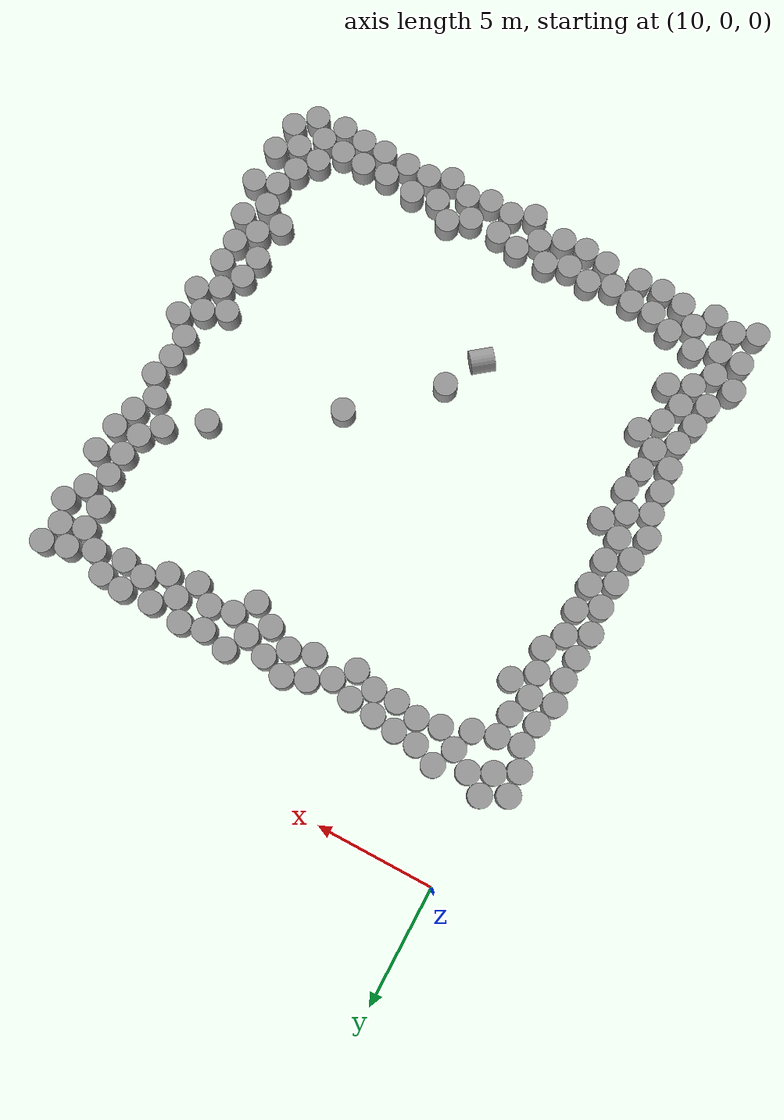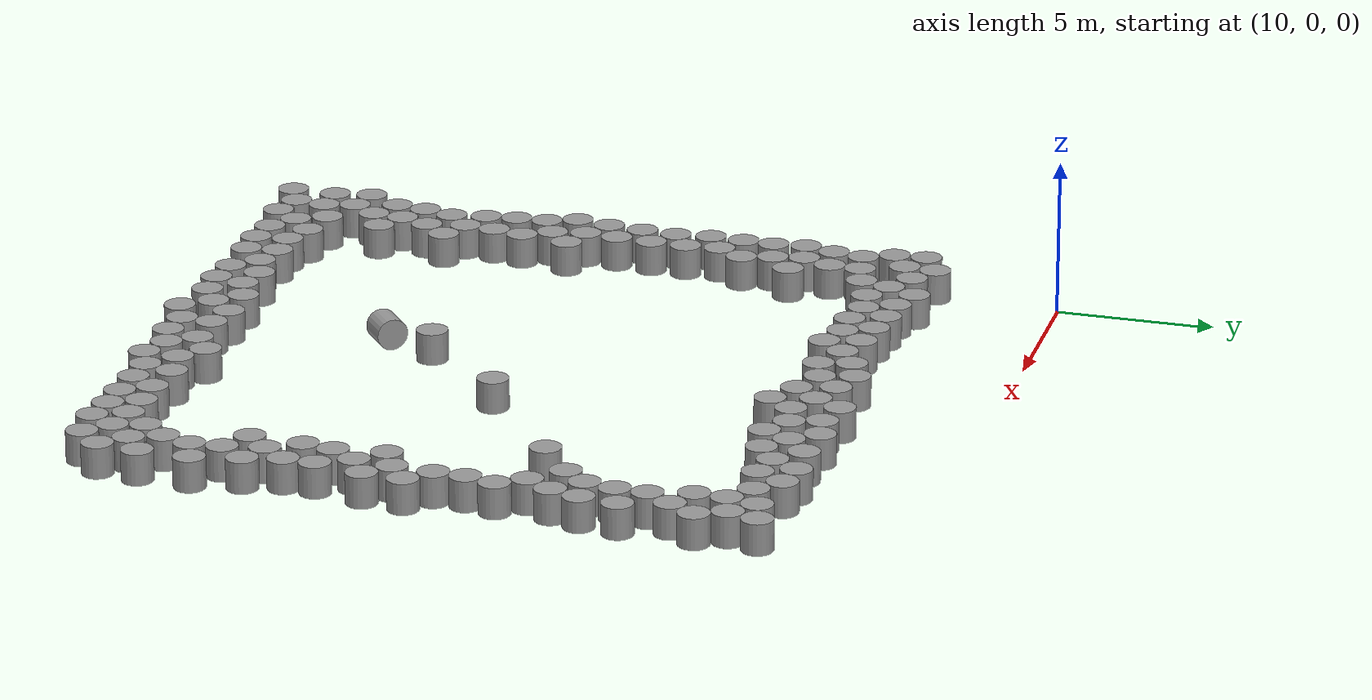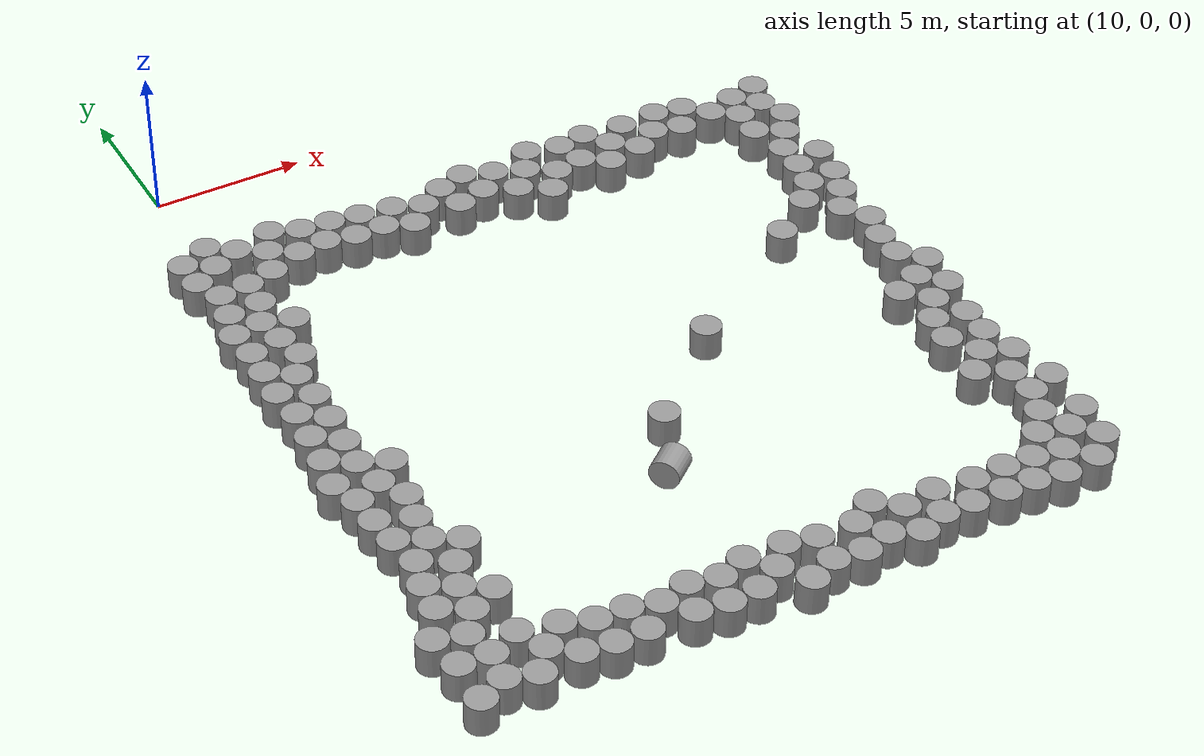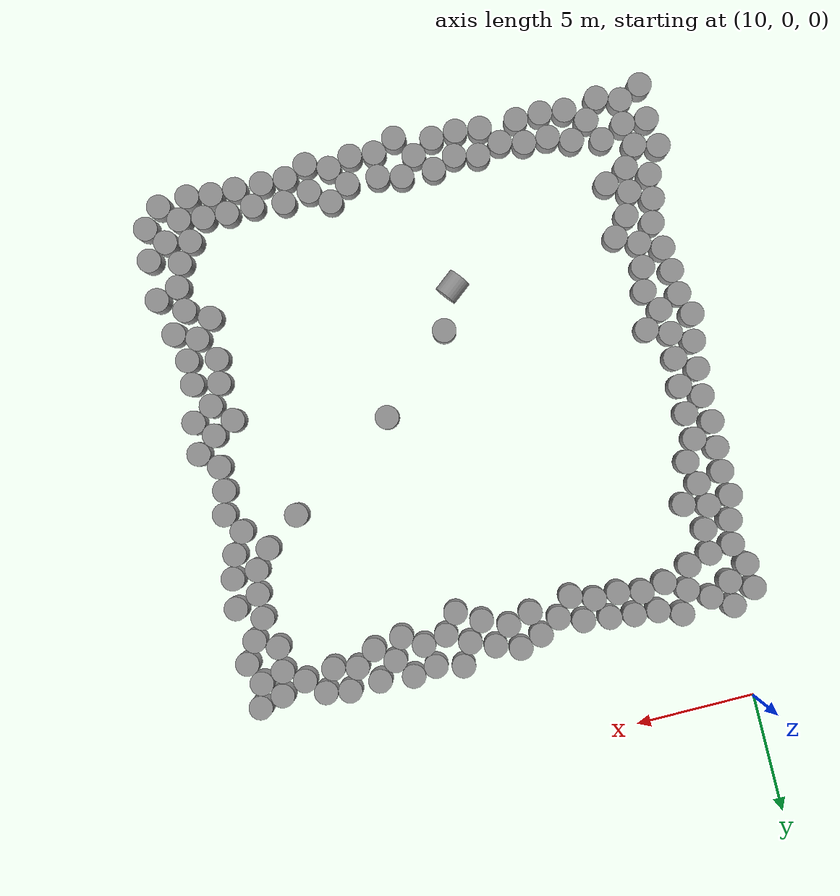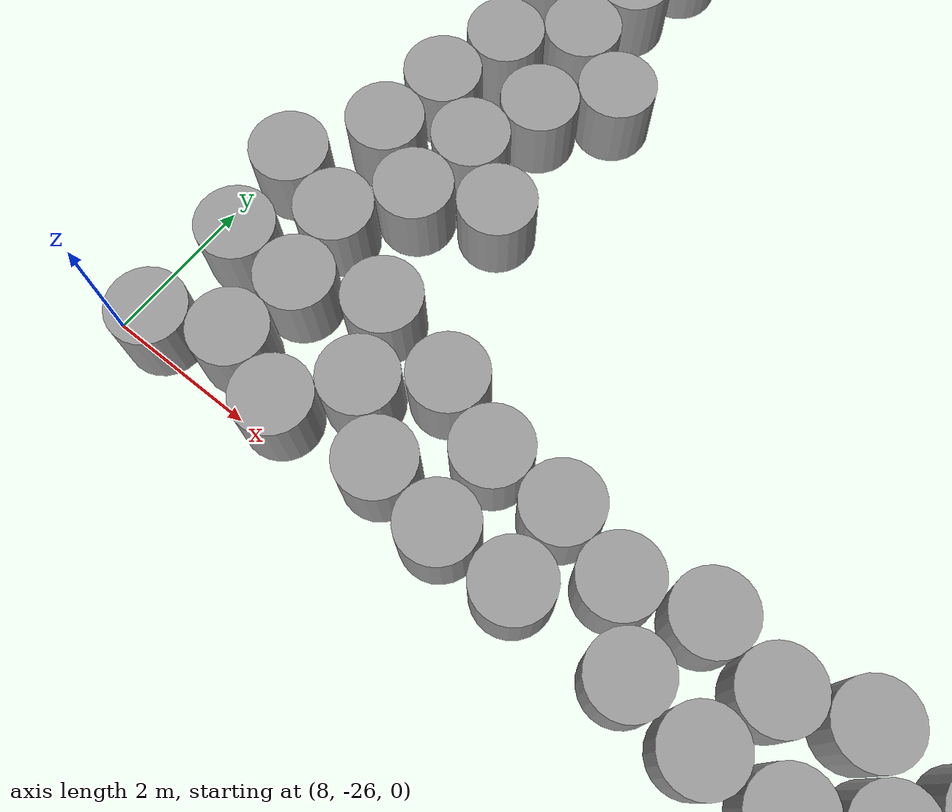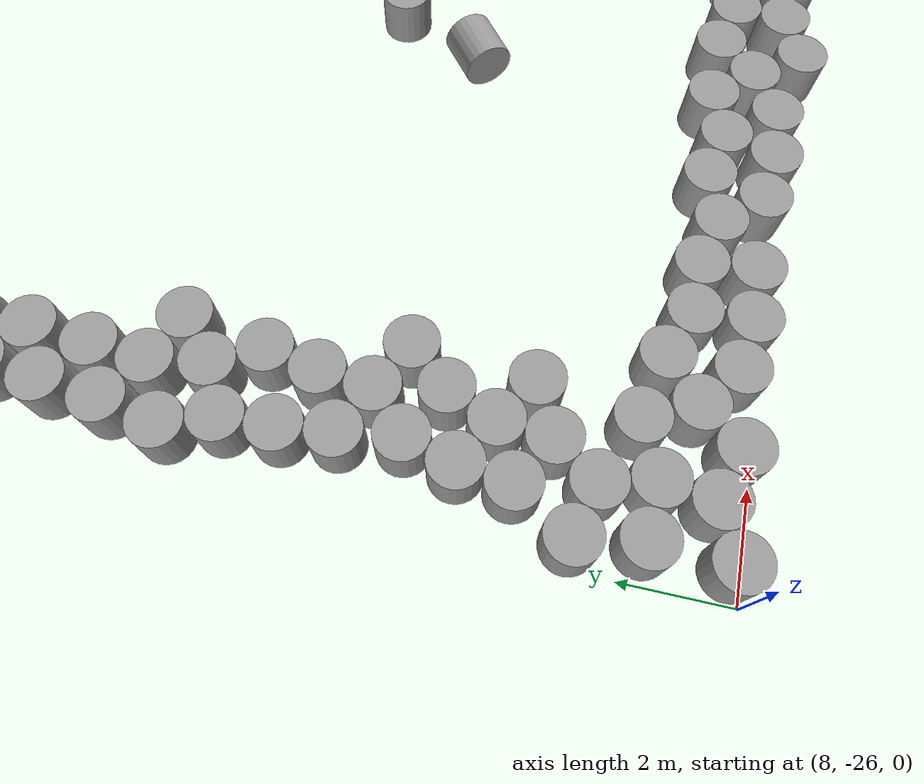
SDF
<sdf version="1.4">
 <world name="default">
  <physics type="ode">
   <gravity>0 0 -9.8</gravity>
   <ode>
    <solver><type>quick</type><iters>40</iters><sor>1.0</sor></solver>
    <constraints>
     <cfm>0.0</cfm>
     <erp>0.2</erp>
     <contact_max_correcting_vel>100.0</contact_max_correcting_vel>
     <contact_surface_layer>0.0</contact_surface_layer>
    </constraints>
   </ode>
   <max_step_size>0.001</max_step_size>
  </physics>
  <light name="sun" type="directional">
   <pose>0 0 10 0 -0 0</pose>
   <diffuse>0.8 0.8 0.8 1</diffuse>
   <specular>0.2 0.2 0.2 1</specular>
   <attenuation>
    <range>1000</range>
    <constant>0.9</constant>
    <linear>0.01</linear>
    <quadratic>0.001</quadratic>
   </attenuation>
   <direction>-0.5 0.1 -0.9</direction>
  </light>
  <model name="ground">
   <link name="body">
    <collision name="geom">
     <geometry><plane><normal>0 0 1</normal><size>1 1</size></plane></geometry>
     <surface><friction><ode><mu>100</mu><mu2>50</mu2></ode></friction></surface>
    </collision>
   </link>
   <static>1</static>
  </model>
  <gravity>0 0 -9.8</gravity>
  <magnetic_field>6e-06 2.3e-05 -4.2e-05</magnetic_field>
  <atmosphere type="adiabatic"/>
  <scene><ambient>0.4 0.4 0.4 1</ambient><background>0.7 0.7 0.7 1</background><shadows>1</shadows></scene>
  <spherical_coordinates>
   <surface_model>EARTH_WGS84</surface_model>
   <latitude_deg>0</latitude_deg>
   <longitude_deg>0</longitude_deg>
   <elevation>0</elevation>
   <heading_deg>0</heading_deg>
  </spherical_coordinates>
  <model name="unit_cylinder">
   <pose>26.8018 -25.697 0.499995 -2e-06 1e-06 0.040756</pose>
   <link name="link">
    <inertial>
     <mass>1</mass>
     <inertia><ixx>0.145833</ixx><ixy>0</ixy><ixz>0</ixz><iyy>0.145833</iyy><iyz>0</iyz><izz>0.125</izz></inertia>
    </inertial>
    <collision name="collision">
     <geometry><cylinder><radius>0.5</radius><length>1</length></cylinder></geometry>
    </collision>
    <visual name="visual">
     <geometry><cylinder><radius>0.5</radius><length>1</length></cylinder></geometry>
     <material>
      <script><name>Gazebo/Grey</name><uri>file://media/materials/scripts/gazebo.material</uri></script>
     </material>
    </visual>
   </link>
  </model>
  <model name="unit_cylinder_clone">
   <pose>27.7903 -25.8482 0.499995 -2e-06 2e-06 0.239846</pose>
   <link name="link">
    <inertial>
     <mass>1</mass>
     <inertia><ixx>0.145833</ixx><ixy>0</ixy><ixz>0</ixz><iyy>0.145833</iyy><iyz>0</iyz><izz>0.125</izz></inertia>
    </inertial>
    <collision name="collision">
     <geometry><cylinder><radius>0.5</radius><length>1</length></cylinder></geometry>
    </collision>
    <visual name="visual">
     <geometry><cylinder><radius>0.5</radius><length>1</length></cylinder></geometry>
     <material>
      <script><name>Gazebo/Grey</name><uri>file://media/materials/scripts/gazebo.material</uri></script>
     </material>
    </visual>
   </link>
  </model>
  <model name="unit_cylinder_clone_0">
   <pose>29.0276 -25.7266 0.499998 3e-06 -3e-06 0.070741</pose>
   <link name="link">
    <inertial>
     <mass>1</mass>
     <inertia><ixx>0.145833</ixx><ixy>0</ixy><ixz>0</ixz><iyy>0.145833</iyy><iyz>0</iyz><izz>0.125</izz></inertia>
    </inertial>
    <collision name="collision">
     <geometry><cylinder><radius>0.5</radius><length>1</length></cylinder></geometry>
    </collision>
    <visual name="visual">
     <geometry><cylinder><radius>0.5</radius><length>1</length></cylinder></geometry>
     <material>
      <script><name>Gazebo/Grey</name><uri>file://media/materials/scripts/gazebo.material</uri></script>
     </material>
    </visual>
   </link>
  </model>
  <model name="unit_cylinder_clone_1">
   <pose>29.7721 -24.9783 0.499998 3e-06 -3e-06 0.079465</pose>
   <link name="link">
    <inertial>
     <mass>1</mass>
     <inertia><ixx>0.145833</ixx><ixy>0</ixy><ixz>0</ixz><iyy>0.145833</iyy><iyz>0</iyz><izz>0.125</izz></inertia>
    </inertial>
    <collision name="collision">
     <geometry><cylinder><radius>0.5</radius><length>1</length></cylinder></geometry>
    </collision>
    <visual name="visual">
     <geometry><cylinder><radius>0.5</radius><length>1</length></cylinder></geometry>
     <material>
      <script><name>Gazebo/Grey</name><uri>file://media/materials/scripts/gazebo.material</uri></script>
     </material>
    </visual>
   </link>
  </model>
  <model name="unit_cylinder_clone_2">
   <pose>29.9412 -23.6675 0.499996 -2e-06 -2e-06 -0.015943</pose>
   <link name="link">
    <inertial>
     <mass>1</mass>
     <inertia><ixx>0.145833</ixx><ixy>0</ixy><ixz>0</ixz><iyy>0.145833</iyy><iyz>0</iyz><izz>0.125</izz></inertia>
    </inertial>
    <collision name="collision">
     <geometry><cylinder><radius>0.5</radius><length>1</length></cylinder></geometry>
    </collision>
    <visual name="visual">
     <geometry><cylinder><radius>0.5</radius><length>1</length></cylinder></geometry>
     <material>
      <script><name>Gazebo/Grey</name><uri>file://media/materials/scripts/gazebo.material</uri></script>
     </material>
    </visual>
   </link>
  </model>
  <model name="unit_cylinder_clone_3">
   <pose>29.0754 -22.3193 0.499995 -3e-06 2e-06 -0.026891</pose>
   <link name="link">
    <inertial>
     <mass>1</mass>
     <inertia><ixx>0.145833</ixx><ixy>0</ixy><ixz>0</ixz><iyy>0.145833</iyy><iyz>0</iyz><izz>0.125</izz></inertia>
    </inertial>
    <collision name="collision">
     <geometry><cylinder><radius>0.5</radius><length>1</length></cylinder></geometry>
    </collision>
    <visual name="visual">
     <geometry><cylinder><radius>0.5</radius><length>1</length></cylinder></geometry>
     <material>
      <script><name>Gazebo/Grey</name><uri>file://media/materials/scripts/gazebo.material</uri></script>
     </material>
    </visual>
   </link>
  </model>
  <model name="unit_cylinder_clone_4">
   <pose>30.0254 -22.0038 0.499991 1e-06 1e-06 0.048586</pose>
   <link name="link">
    <inertial>
     <mass>1</mass>
     <inertia><ixx>0.145833</ixx><ixy>0</ixy><ixz>0</ixz><iyy>0.145833</iyy><iyz>0</iyz><izz>0.125</izz></inertia>
    </inertial>
    <collision name="collision">
     <geometry><cylinder><radius>0.5</radius><length>1</length></cylinder></geometry>
    </collision>
    <visual name="visual">
     <geometry><cylinder><radius>0.5</radius><length>1</length></cylinder></geometry>
     <material>
      <script><name>Gazebo/Grey</name><uri>file://media/materials/scripts/gazebo.material</uri></script>
     </material>
    </visual>
   </link>
  </model>
  <model name="unit_cylinder_clone_5">
   <pose>28.7866 -20.0533 0.499994 3e-06 1e-06 0.262651</pose>
   <link name="link">
    <inertial>
     <mass>1</mass>
     <inertia><ixx>0.145833</ixx><ixy>0</ixy><ixz>0</ixz><iyy>0.145833</iyy><iyz>0</iyz><izz>0.125</izz></inertia>
    </inertial>
    <collision name="collision">
     <geometry><cylinder><radius>0.5</radius><length>1</length></cylinder></geometry>
    </collision>
    <visual name="visual">
     <geometry><cylinder><radius>0.5</radius><length>1</length></cylinder></geometry>
     <material>
      <script><name>Gazebo/Grey</name><uri>file://media/materials/scripts/gazebo.material</uri></script>
     </material>
    </visual>
   </link>
  </model>
  <model name="unit_cylinder_clone_6">
   <pose>29.6989 -20.4656 0.499994 2e-06 1e-06 0.126498</pose>
   <link name="link">
    <inertial>
     <mass>1</mass>
     <inertia><ixx>0.145833</ixx><ixy>0</ixy><ixz>0</ixz><iyy>0.145833</iyy><iyz>0</iyz><izz>0.125</izz></inertia>
    </inertial>
    <collision name="collision">
     <geometry><cylinder><radius>0.5</radius><length>1</length></cylinder></geometry>
    </collision>
    <visual name="visual">
     <geometry><cylinder><radius>0.5</radius><length>1</length></cylinder></geometry>
     <material>
      <script><name>Gazebo/Grey</name><uri>file://media/materials/scripts/gazebo.material</uri></script>
     </material>
    </visual>
   </link>
  </model>
  <model name="unit_cylinder_clone_7">
   <pose>29.4174 -19.2771 0.499996 -2e-06 -2e-06 -0.230884</pose>
   <link name="link">
    <inertial>
     <mass>1</mass>
     <inertia><ixx>0.145833</ixx><ixy>0</ixy><ixz>0</ixz><iyy>0.145833</iyy><iyz>0</iyz><izz>0.125</izz></inertia>
    </inertial>
    <collision name="collision">
     <geometry><cylinder><radius>0.5</radius><length>1</length></cylinder></geometry>
    </collision>
    <visual name="visual">
     <geometry><cylinder><radius>0.5</radius><length>1</length></cylinder></geometry>
     <material>
      <script><name>Gazebo/Grey</name><uri>file://media/materials/scripts/gazebo.material</uri></script>
     </material>
    </visual>
   </link>
  </model>
  <model name="unit_cylinder_clone_8">
   <pose>28.9294 -17.2288 0.499999 2e-06 2e-06 0.123514</pose>
   <link name="link">
    <inertial>
     <mass>1</mass>
     <inertia><ixx>0.145833</ixx><ixy>0</ixy><ixz>0</ixz><iyy>0.145833</iyy><iyz>0</iyz><izz>0.125</izz></inertia>
    </inertial>
    <collision name="collision">
     <geometry><cylinder><radius>0.5</radius><length>1</length></cylinder></geometry>
    </collision>
    <visual name="visual">
     <geometry><cylinder><radius>0.5</radius><length>1</length></cylinder></geometry>
     <material>
      <script><name>Gazebo/Grey</name><uri>file://media/materials/scripts/gazebo.material</uri></script>
     </material>
    </visual>
   </link>
  </model>
  <model name="unit_cylinder_clone_9">
   <pose>29.795 -16.7274 0.499991 1e-06 1e-06 0.099586</pose>
   <link name="link">
    <inertial>
     <mass>1</mass>
     <inertia><ixx>0.145833</ixx><ixy>0</ixy><ixz>0</ixz><iyy>0.145833</iyy><iyz>0</iyz><izz>0.125</izz></inertia>
    </inertial>
    <collision name="collision">
     <geometry><cylinder><radius>0.5</radius><length>1</length></cylinder></geometry>
    </collision>
    <visual name="visual">
     <geometry><cylinder><radius>0.5</radius><length>1</length></cylinder></geometry>
     <material>
      <script><name>Gazebo/Grey</name><uri>file://media/materials/scripts/gazebo.material</uri></script>
     </material>
    </visual>
   </link>
  </model>
  <model name="unit_cylinder_clone_10">
   <pose>29.9089 -15.4151 0.499994 2e-06 2e-06 -0.025586</pose>
   <link name="link">
    <inertial>
     <mass>1</mass>
     <inertia><ixx>0.145833</ixx><ixy>0</ixy><ixz>0</ixz><iyy>0.145833</iyy><iyz>0</iyz><izz>0.125</izz></inertia>
    </inertial>
    <collision name="collision">
     <geometry><cylinder><radius>0.5</radius><length>1</length></cylinder></geometry>
    </collision>
    <visual name="visual">
     <geometry><cylinder><radius>0.5</radius><length>1</length></cylinder></geometry>
     <material>
      <script><name>Gazebo/Grey</name><uri>file://media/materials/scripts/gazebo.material</uri></script>
     </material>
    </visual>
   </link>
  </model>
  <model name="unit_cylinder_clone_11">
   <pose>29.2485 -13.695 0.499992 3e-06 -2e-06 -0.063354</pose>
   <link name="link">
    <inertial>
     <mass>1</mass>
     <inertia><ixx>0.145833</ixx><ixy>0</ixy><ixz>0</ixz><iyy>0.145833</iyy><iyz>0</iyz><izz>0.125</izz></inertia>
    </inertial>
    <collision name="collision">
     <geometry><cylinder><radius>0.5</radius><length>1</length></cylinder></geometry>
    </collision>
    <visual name="visual">
     <geometry><cylinder><radius>0.5</radius><length>1</length></cylinder></geometry>
     <material>
      <script><name>Gazebo/Grey</name><uri>file://media/materials/scripts/gazebo.material</uri></script>
     </material>
    </visual>
   </link>
  </model>
  <model name="unit_cylinder_clone_12">
   <pose>28.962 -11.8819 0.499999 2e-06 2e-06 -0.093312</pose>
   <link name="link">
    <inertial>
     <mass>1</mass>
     <inertia><ixx>0.145833</ixx><ixy>0</ixy><ixz>0</ixz><iyy>0.145833</iyy><iyz>0</iyz><izz>0.125</izz></inertia>
    </inertial>
    <collision name="collision">
     <geometry><cylinder><radius>0.5</radius><length>1</length></cylinder></geometry>
    </collision>
    <visual name="visual">
     <geometry><cylinder><radius>0.5</radius><length>1</length></cylinder></geometry>
     <material>
      <script><name>Gazebo/Grey</name><uri>file://media/materials/scripts/gazebo.material</uri></script>
     </material>
    </visual>
   </link>
  </model>
  <model name="unit_cylinder_clone_13">
   <pose>29.4829 -11.0275 0.499996 -2e-06 -2e-06 0.048416</pose>
   <link name="link">
    <inertial>
     <mass>1</mass>
     <inertia><ixx>0.145833</ixx><ixy>0</ixy><ixz>0</ixz><iyy>0.145833</iyy><iyz>0</iyz><izz>0.125</izz></inertia>
    </inertial>
    <collision name="collision">
     <geometry><cylinder><radius>0.5</radius><length>1</length></cylinder></geometry>
    </collision>
    <visual name="visual">
     <geometry><cylinder><radius>0.5</radius><length>1</length></cylinder></geometry>
     <material>
      <script><name>Gazebo/Grey</name><uri>file://media/materials/scripts/gazebo.material</uri></script>
     </material>
    </visual>
   </link>
  </model>
  <model name="unit_cylinder_clone_14">
   <pose>29.7953 -10.0764 0.5 -1e-06 -1e-06 0.176348</pose>
   <link name="link">
    <inertial>
     <mass>1</mass>
     <inertia><ixx>0.145833</ixx><ixy>0</ixy><ixz>0</ixz><iyy>0.145833</iyy><iyz>0</iyz><izz>0.125</izz></inertia>
    </inertial>
    <collision name="collision">
     <geometry><cylinder><radius>0.5</radius><length>1</length></cylinder></geometry>
    </collision>
    <visual name="visual">
     <geometry><cylinder><radius>0.5</radius><length>1</length></cylinder></geometry>
     <material>
      <script><name>Gazebo/Grey</name><uri>file://media/materials/scripts/gazebo.material</uri></script>
     </material>
    </visual>
   </link>
  </model>
  <model name="unit_cylinder_clone_15">
   <pose>29.5551 -7.37609 0.499995 -2e-06 2e-06 0.059194</pose>
   <link name="link">
    <inertial>
     <mass>1</mass>
     <inertia><ixx>0.145833</ixx><ixy>0</ixy><ixz>0</ixz><iyy>0.145833</iyy><iyz>0</iyz><izz>0.125</izz></inertia>
    </inertial>
    <collision name="collision">
     <geometry><cylinder><radius>0.5</radius><length>1</length></cylinder></geometry>
    </collision>
    <visual name="visual">
     <geometry><cylinder><radius>0.5</radius><length>1</length></cylinder></geometry>
     <material>
      <script><name>Gazebo/Grey</name><uri>file://media/materials/scripts/gazebo.material</uri></script>
     </material>
    </visual>
   </link>
  </model>
  <model name="unit_cylinder_clone_16">
   <pose>30.0751 -6.51711 0.499995 -2e-06 2e-06 0.108755</pose>
   <link name="link">
    <inertial>
     <mass>1</mass>
     <inertia><ixx>0.145833</ixx><ixy>0</ixy><ixz>0</ixz><iyy>0.145833</iyy><iyz>0</iyz><izz>0.125</izz></inertia>
    </inertial>
    <collision name="collision">
     <geometry><cylinder><radius>0.5</radius><length>1</length></cylinder></geometry>
    </collision>
    <visual name="visual">
     <geometry><cylinder><radius>0.5</radius><length>1</length></cylinder></geometry>
     <material>
      <script><name>Gazebo/Grey</name><uri>file://media/materials/scripts/gazebo.material</uri></script>
     </material>
    </visual>
   </link>
  </model>
  <model name="unit_cylinder_clone_17">
   <pose>29.976 -4.63218 0.499998 3e-06 3e-06 0.009053</pose>
   <link name="link">
    <inertial>
     <mass>1</mass>
     <inertia><ixx>0.145833</ixx><ixy>0</ixy><ixz>0</ixz><iyy>0.145833</iyy><iyz>0</iyz><izz>0.125</izz></inertia>
    </inertial>
    <collision name="collision">
     <geometry><cylinder><radius>0.5</radius><length>1</length></cylinder></geometry>
    </collision>
    <visual name="visual">
     <geometry><cylinder><radius>0.5</radius><length>1</length></cylinder></geometry>
     <material>
      <script><name>Gazebo/Grey</name><uri>file://media/materials/scripts/gazebo.material</uri></script>
     </material>
    </visual>
   </link>
  </model>
  <model name="unit_cylinder_clone_18">
   <pose>29.4978 -12.7265 0.5 -1e-06 -1e-06 0.051015</pose>
   <link name="link">
    <inertial>
     <mass>1</mass>
     <inertia><ixx>0.145833</ixx><ixy>0</ixy><ixz>0</ixz><iyy>0.145833</iyy><iyz>0</iyz><izz>0.125</izz></inertia>
    </inertial>
    <collision name="collision">
     <geometry><cylinder><radius>0.5</radius><length>1</length></cylinder></geometry>
    </collision>
    <visual name="visual">
     <geometry><cylinder><radius>0.5</radius><length>1</length></cylinder></geometry>
     <material>
      <script><name>Gazebo/Grey</name><uri>file://media/materials/scripts/gazebo.material</uri></script>
     </material>
    </visual>
   </link>
  </model>
  <model name="unit_cylinder_clone_19">
   <pose>29.4623 -18.2774 0.499994 2e-06 2e-06 -0.124848</pose>
   <link name="link">
    <inertial>
     <mass>1</mass>
     <inertia><ixx>0.145833</ixx><ixy>0</ixy><ixz>0</ixz><iyy>0.145833</iyy><iyz>0</iyz><izz>0.125</izz></inertia>
    </inertial>
    <collision name="collision">
     <geometry><cylinder><radius>0.5</radius><length>1</length></cylinder></geometry>
    </collision>
    <visual name="visual">
     <geometry><cylinder><radius>0.5</radius><length>1</length></cylinder></geometry>
     <material>
      <script><name>Gazebo/Grey</name><uri>file://media/materials/scripts/gazebo.material</uri></script>
     </material>
    </visual>
   </link>
  </model>
  <model name="unit_cylinder_clone_20">
   <pose>29.9729 -8.84857 0.501364 -0.001233 -0.002452 2.3335</pose>
   <link name="link">
    <inertial>
     <mass>1</mass>
     <inertia><ixx>0.145833</ixx><ixy>0</ixy><ixz>0</ixz><iyy>0.145833</iyy><iyz>0</iyz><izz>0.125</izz></inertia>
    </inertial>
    <collision name="collision">
     <geometry><cylinder><radius>0.5</radius><length>1</length></cylinder></geometry>
    </collision>
    <visual name="visual">
     <geometry><cylinder><radius>0.5</radius><length>1</length></cylinder></geometry>
     <material>
      <script><name>Gazebo/Grey</name><uri>file://media/materials/scripts/gazebo.material</uri></script>
     </material>
    </visual>
   </link>
  </model>
  <model name="unit_cylinder_clone_21">
   <pose>28.9761 -4.89449 0.5 -1e-06 -1e-06 -0.038363</pose>
   <link name="link">
    <inertial>
     <mass>1</mass>
     <inertia><ixx>0.145833</ixx><ixy>0</ixy><ixz>0</ixz><iyy>0.145833</iyy><iyz>0</iyz><izz>0.125</izz></inertia>
    </inertial>
    <collision name="collision">
     <geometry><cylinder><radius>0.5</radius><length>1</length></cylinder></geometry>
    </collision>
    <visual name="visual">
     <geometry><cylinder><radius>0.5</radius><length>1</length></cylinder></geometry>
     <material>
      <script><name>Gazebo/Grey</name><uri>file://media/materials/scripts/gazebo.material</uri></script>
     </material>
    </visual>
   </link>
  </model>
  <model name="unit_cylinder_clone_22">
   <pose>27.2072 -4.58034 0.499995 -2e-06 1e-06 0.0063</pose>
   <link name="link">
    <inertial>
     <mass>1</mass>
     <inertia><ixx>0.145833</ixx><ixy>0</ixy><ixz>0</ixz><iyy>0.145833</iyy><iyz>0</iyz><izz>0.125</izz></inertia>
    </inertial>
    <collision name="collision">
     <geometry><cylinder><radius>0.5</radius><length>1</length></cylinder></geometry>
    </collision>
    <visual name="visual">
     <geometry><cylinder><radius>0.5</radius><length>1</length></cylinder></geometry>
     <material>
      <script><name>Gazebo/Grey</name><uri>file://media/materials/scripts/gazebo.material</uri></script>
     </material>
    </visual>
   </link>
  </model>
  <model name="unit_cylinder_clone_23">
   <pose>26.2217 -4.41 0.499995 -2e-06 2e-06 0.037885</pose>
   <link name="link">
    <inertial>
     <mass>1</mass>
     <inertia><ixx>0.145833</ixx><ixy>0</ixy><ixz>0</ixz><iyy>0.145833</iyy><iyz>0</iyz><izz>0.125</izz></inertia>
    </inertial>
    <collision name="collision">
     <geometry><cylinder><radius>0.5</radius><length>1</length></cylinder></geometry>
    </collision>
    <visual name="visual">
     <geometry><cylinder><radius>0.5</radius><length>1</length></cylinder></geometry>
     <material>
      <script><name>Gazebo/Grey</name><uri>file://media/materials/scripts/gazebo.material</uri></script>
     </material>
    </visual>
   </link>
  </model>
  <model name="unit_cylinder_clone_24">
   <pose>24.9179 -4.50219 0.5034 -0.004635 0.005014 -0.097426</pose>
   <link name="link">
    <inertial>
     <mass>1</mass>
     <inertia><ixx>0.145833</ixx><ixy>0</ixy><ixz>0</ixz><iyy>0.145833</iyy><iyz>0</iyz><izz>0.125</izz></inertia>
    </inertial>
    <collision name="collision">
     <geometry><cylinder><radius>0.5</radius><length>1</length></cylinder></geometry>
    </collision>
    <visual name="visual">
     <geometry><cylinder><radius>0.5</radius><length>1</length></cylinder></geometry>
     <material>
      <script><name>Gazebo/Grey</name><uri>file://media/materials/scripts/gazebo.material</uri></script>
     </material>
    </visual>
   </link>
  </model>
  <model name="unit_cylinder_clone_25">
   <pose>23.5263 -4.35552 0.499999 2e-06 2e-06 0.013764</pose>
   <link name="link">
    <inertial>
     <mass>1</mass>
     <inertia><ixx>0.145833</ixx><ixy>0</ixy><ixz>0</ixz><iyy>0.145833</iyy><iyz>0</iyz><izz>0.125</izz></inertia>
    </inertial>
    <collision name="collision">
     <geometry><cylinder><radius>0.5</radius><length>1</length></cylinder></geometry>
    </collision>
    <visual name="visual">
     <geometry><cylinder><radius>0.5</radius><length>1</length></cylinder></geometry>
     <material>
      <script><name>Gazebo/Grey</name><uri>file://media/materials/scripts/gazebo.material</uri></script>
     </material>
    </visual>
   </link>
  </model>
  <model name="unit_cylinder_clone_26">
   <pose>22.5414 -4.53228 0.499992 -4e-06 -2e-06 0.240591</pose>
   <link name="link">
    <inertial>
     <mass>1</mass>
     <inertia><ixx>0.145833</ixx><ixy>0</ixy><ixz>0</ixz><iyy>0.145833</iyy><iyz>0</iyz><izz>0.125</izz></inertia>
    </inertial>
    <collision name="collision">
     <geometry><cylinder><radius>0.5</radius><length>1</length></cylinder></geometry>
    </collision>
    <visual name="visual">
     <geometry><cylinder><radius>0.5</radius><length>1</length></cylinder></geometry>
     <material>
      <script><name>Gazebo/Grey</name><uri>file://media/materials/scripts/gazebo.material</uri></script>
     </material>
    </visual>
   </link>
  </model>
  <model name="unit_cylinder_clone_27">
   <pose>21.43 -4.26292 0.50074 -0.001458 -0.000297 0.034988</pose>
   <link name="link">
    <inertial>
     <mass>1</mass>
     <inertia><ixx>0.145833</ixx><ixy>0</ixy><ixz>0</ixz><iyy>0.145833</iyy><iyz>0</iyz><izz>0.125</izz></inertia>
    </inertial>
    <collision name="collision">
     <geometry><cylinder><radius>0.5</radius><length>1</length></cylinder></geometry>
    </collision>
    <visual name="visual">
     <geometry><cylinder><radius>0.5</radius><length>1</length></cylinder></geometry>
     <material>
      <script><name>Gazebo/Grey</name><uri>file://media/materials/scripts/gazebo.material</uri></script>
     </material>
    </visual>
   </link>
  </model>
  <model name="unit_cylinder_clone_28">
   <pose>19.9431 -4.7481 0.5 0 0 -0.131843</pose>
   <link name="link">
    <inertial>
     <mass>1</mass>
     <inertia><ixx>0.145833</ixx><ixy>0</ixy><ixz>0</ixz><iyy>0.145833</iyy><iyz>0</iyz><izz>0.125</izz></inertia>
    </inertial>
    <collision name="collision">
     <geometry><cylinder><radius>0.5</radius><length>1</length></cylinder></geometry>
    </collision>
    <visual name="visual">
     <geometry><cylinder><radius>0.5</radius><length>1</length></cylinder></geometry>
     <material>
      <script><name>Gazebo/Grey</name><uri>file://media/materials/scripts/gazebo.material</uri></script>
     </material>
    </visual>
   </link>
  </model>
  <model name="unit_cylinder_clone_29">
   <pose>18.9579 -4.39646 0.499994 2e-06 1e-06 0.172267</pose>
   <link name="link">
    <inertial>
     <mass>1</mass>
     <inertia><ixx>0.145833</ixx><ixy>0</ixy><ixz>0</ixz><iyy>0.145833</iyy><iyz>0</iyz><izz>0.125</izz></inertia>
    </inertial>
    <collision name="collision">
     <geometry><cylinder><radius>0.5</radius><length>1</length></cylinder></geometry>
    </collision>
    <visual name="visual">
     <geometry><cylinder><radius>0.5</radius><length>1</length></cylinder></geometry>
     <material>
      <script><name>Gazebo/Grey</name><uri>file://media/materials/scripts/gazebo.material</uri></script>
     </material>
    </visual>
   </link>
  </model>
  <model name="unit_cylinder_clone_30">
   <pose>17.1453 -5.23012 0.499999 2e-06 2e-06 0.191595</pose>
   <link name="link">
    <inertial>
     <mass>1</mass>
     <inertia><ixx>0.145833</ixx><ixy>0</ixy><ixz>0</ixz><iyy>0.145833</iyy><iyz>0</iyz><izz>0.125</izz></inertia>
    </inertial>
    <collision name="collision">
     <geometry><cylinder><radius>0.5</radius><length>1</length></cylinder></geometry>
    </collision>
    <visual name="visual">
     <geometry><cylinder><radius>0.5</radius><length>1</length></cylinder></geometry>
     <material>
      <script><name>Gazebo/Grey</name><uri>file://media/materials/scripts/gazebo.material</uri></script>
     </material>
    </visual>
   </link>
  </model>
  <model name="unit_cylinder_clone_31">
   <pose>18.012 -4.72658 0.499996 -2e-06 -2e-06 -0.131609</pose>
   <link name="link">
    <inertial>
     <mass>1</mass>
     <inertia><ixx>0.145833</ixx><ixy>0</ixy><ixz>0</ixz><iyy>0.145833</iyy><iyz>0</iyz><izz>0.125</izz></inertia>
    </inertial>
    <collision name="collision">
     <geometry><cylinder><radius>0.5</radius><length>1</length></cylinder></geometry>
    </collision>
    <visual name="visual">
     <geometry><cylinder><radius>0.5</radius><length>1</length></cylinder></geometry>
     <material>
      <script><name>Gazebo/Grey</name><uri>file://media/materials/scripts/gazebo.material</uri></script>
     </material>
    </visual>
   </link>
  </model>
  <model name="unit_cylinder_clone_32">
   <pose>16.1717 -4.87234 0.499999 2e-06 2e-06 0.030905</pose>
   <link name="link">
    <inertial>
     <mass>1</mass>
     <inertia><ixx>0.145833</ixx><ixy>0</ixy><ixz>0</ixz><iyy>0.145833</iyy><iyz>0</iyz><izz>0.125</izz></inertia>
    </inertial>
    <collision name="collision">
     <geometry><cylinder><radius>0.5</radius><length>1</length></cylinder></geometry>
    </collision>
    <visual name="visual">
     <geometry><cylinder><radius>0.5</radius><length>1</length></cylinder></geometry>
     <material>
      <script><name>Gazebo/Grey</name><uri>file://media/materials/scripts/gazebo.material</uri></script>
     </material>
    </visual>
   </link>
  </model>
  <model name="unit_cylinder_clone_33">
   <pose>14.0804 -4.59788 0.499991 1e-06 1e-06 0.07608</pose>
   <link name="link">
    <inertial>
     <mass>1</mass>
     <inertia><ixx>0.145833</ixx><ixy>0</ixy><ixz>0</ixz><iyy>0.145833</iyy><iyz>0</iyz><izz>0.125</izz></inertia>
    </inertial>
    <collision name="collision">
     <geometry><cylinder><radius>0.5</radius><length>1</length></cylinder></geometry>
    </collision>
    <visual name="visual">
     <geometry><cylinder><radius>0.5</radius><length>1</length></cylinder></geometry>
     <material>
      <script><name>Gazebo/Grey</name><uri>file://media/materials/scripts/gazebo.material</uri></script>
     </material>
    </visual>
   </link>
  </model>
  <model name="unit_cylinder_clone_34">
   <pose>12.141 -4.13683 0.499995 -2e-06 2e-06 -0.020771</pose>
   <link name="link">
    <inertial>
     <mass>1</mass>
     <inertia><ixx>0.145833</ixx><ixy>0</ixy><ixz>0</ixz><iyy>0.145833</iyy><iyz>0</iyz><izz>0.125</izz></inertia>
    </inertial>
    <collision name="collision">
     <geometry><cylinder><radius>0.5</radius><length>1</length></cylinder></geometry>
    </collision>
    <visual name="visual">
     <geometry><cylinder><radius>0.5</radius><length>1</length></cylinder></geometry>
     <material>
      <script><name>Gazebo/Grey</name><uri>file://media/materials/scripts/gazebo.material</uri></script>
     </material>
    </visual>
   </link>
  </model>
  <model name="unit_cylinder_clone_35">
   <pose>9.99479 -3.9577 0.499996 2e-06 -2e-06 0.001622</pose>
   <link name="link">
    <inertial>
     <mass>1</mass>
     <inertia><ixx>0.145833</ixx><ixy>0</ixy><ixz>0</ixz><iyy>0.145833</iyy><iyz>0</iyz><izz>0.125</izz></inertia>
    </inertial>
    <collision name="collision">
     <geometry><cylinder><radius>0.5</radius><length>1</length></cylinder></geometry>
    </collision>
    <visual name="visual">
     <geometry><cylinder><radius>0.5</radius><length>1</length></cylinder></geometry>
     <material>
      <script><name>Gazebo/Grey</name><uri>file://media/materials/scripts/gazebo.material</uri></script>
     </material>
    </visual>
   </link>
  </model>
  <model name="unit_cylinder_clone_36">
   <pose>9.01163 -4.46893 0.499995 2e-06 -2e-06 0.006356</pose>
   <link name="link">
    <inertial>
     <mass>1</mass>
     <inertia><ixx>0.145833</ixx><ixy>0</ixy><ixz>0</ixz><iyy>0.145833</iyy><iyz>0</iyz><izz>0.125</izz></inertia>
    </inertial>
    <collision name="collision">
     <geometry><cylinder><radius>0.5</radius><length>1</length></cylinder></geometry>
    </collision>
    <visual name="visual">
     <geometry><cylinder><radius>0.5</radius><length>1</length></cylinder></geometry>
     <material>
      <script><name>Gazebo/Grey</name><uri>file://media/materials/scripts/gazebo.material</uri></script>
     </material>
    </visual>
   </link>
  </model>
  <model name="unit_cylinder_clone_37">
   <pose>9.06382 -5.49392 0.499999 2e-06 2e-06 -0.090692</pose>
   <link name="link">
    <inertial>
     <mass>1</mass>
     <inertia><ixx>0.145833</ixx><ixy>0</ixy><ixz>0</ixz><iyy>0.145833</iyy><iyz>0</iyz><izz>0.125</izz></inertia>
    </inertial>
    <collision name="collision">
     <geometry><cylinder><radius>0.5</radius><length>1</length></cylinder></geometry>
    </collision>
    <visual name="visual">
     <geometry><cylinder><radius>0.5</radius><length>1</length></cylinder></geometry>
     <material>
      <script><name>Gazebo/Grey</name><uri>file://media/materials/scripts/gazebo.material</uri></script>
     </material>
    </visual>
   </link>
  </model>
  <model name="unit_cylinder_clone_38">
   <pose>25.8021 -25.673 0.499991 1e-06 1e-06 -0.062745</pose>
   <link name="link">
    <inertial>
     <mass>1</mass>
     <inertia><ixx>0.145833</ixx><ixy>0</ixy><ixz>0</ixz><iyy>0.145833</iyy><iyz>0</iyz><izz>0.125</izz></inertia>
    </inertial>
    <collision name="collision">
     <geometry><cylinder><radius>0.5</radius><length>1</length></cylinder></geometry>
    </collision>
    <visual name="visual">
     <geometry><cylinder><radius>0.5</radius><length>1</length></cylinder></geometry>
     <material>
      <script><name>Gazebo/Grey</name><uri>file://media/materials/scripts/gazebo.material</uri></script>
     </material>
    </visual>
   </link>
  </model>
  <model name="unit_cylinder_clone_39">
   <pose>24.6782 -25.6293 0.5 -1e-06 -1e-06 0.085528</pose>
   <link name="link">
    <inertial>
     <mass>1</mass>
     <inertia><ixx>0.145833</ixx><ixy>0</ixy><ixz>0</ixz><iyy>0.145833</iyy><iyz>0</iyz><izz>0.125</izz></inertia>
    </inertial>
    <collision name="collision">
     <geometry><cylinder><radius>0.5</radius><length>1</length></cylinder></geometry>
    </collision>
    <visual name="visual">
     <geometry><cylinder><radius>0.5</radius><length>1</length></cylinder></geometry>
     <material>
      <script><name>Gazebo/Grey</name><uri>file://media/materials/scripts/gazebo.material</uri></script>
     </material>
    </visual>
   </link>
  </model>
  <model name="unit_cylinder_clone_40">
   <pose>23.677 -25.5955 0.499992 -3e-06 -2e-06 0.112481</pose>
   <link name="link">
    <inertial>
     <mass>1</mass>
     <inertia><ixx>0.145833</ixx><ixy>0</ixy><ixz>0</ixz><iyy>0.145833</iyy><iyz>0</iyz><izz>0.125</izz></inertia>
    </inertial>
    <collision name="collision">
     <geometry><cylinder><radius>0.5</radius><length>1</length></cylinder></geometry>
    </collision>
    <visual name="visual">
     <geometry><cylinder><radius>0.5</radius><length>1</length></cylinder></geometry>
     <material>
      <script><name>Gazebo/Grey</name><uri>file://media/materials/scripts/gazebo.material</uri></script>
     </material>
    </visual>
   </link>
  </model>
  <model name="unit_cylinder_clone_41">
   <pose>21.8206 -25.5633 0.499996 -2e-06 -2e-06 -0.178196</pose>
   <link name="link">
    <inertial>
     <mass>1</mass>
     <inertia><ixx>0.145833</ixx><ixy>0</ixy><ixz>0</ixz><iyy>0.145833</iyy><iyz>0</iyz><izz>0.125</izz></inertia>
    </inertial>
    <collision name="collision">
     <geometry><cylinder><radius>0.5</radius><length>1</length></cylinder></geometry>
    </collision>
    <visual name="visual">
     <geometry><cylinder><radius>0.5</radius><length>1</length></cylinder></geometry>
     <material>
      <script><name>Gazebo/Grey</name><uri>file://media/materials/scripts/gazebo.material</uri></script>
     </material>
    </visual>
   </link>
  </model>
  <model name="unit_cylinder_clone_42">
   <pose>20.8579 -25.834 0.5 0 0 -0.299492</pose>
   <link name="link">
    <inertial>
     <mass>1</mass>
     <inertia><ixx>0.145833</ixx><ixy>0</ixy><ixz>0</ixz><iyy>0.145833</iyy><iyz>0</iyz><izz>0.125</izz></inertia>
    </inertial>
    <collision name="collision">
     <geometry><cylinder><radius>0.5</radius><length>1</length></cylinder></geometry>
    </collision>
    <visual name="visual">
     <geometry><cylinder><radius>0.5</radius><length>1</length></cylinder></geometry>
     <material>
      <script><name>Gazebo/Grey</name><uri>file://media/materials/scripts/gazebo.material</uri></script>
     </material>
    </visual>
   </link>
  </model>
  <model name="unit_cylinder_clone_43">
   <pose>18.9197 -26.1093 0.51184 0.009366 -0.022071 2.09487</pose>
   <link name="link">
    <inertial>
     <mass>1</mass>
     <inertia><ixx>0.145833</ixx><ixy>0</ixy><ixz>0</ixz><iyy>0.145833</iyy><iyz>0</iyz><izz>0.125</izz></inertia>
    </inertial>
    <collision name="collision">
     <geometry><cylinder><radius>0.5</radius><length>1</length></cylinder></geometry>
    </collision>
    <visual name="visual">
     <geometry><cylinder><radius>0.5</radius><length>1</length></cylinder></geometry>
     <material>
      <script><name>Gazebo/Grey</name><uri>file://media/materials/scripts/gazebo.material</uri></script>
     </material>
    </visual>
   </link>
  </model>
  <model name="unit_cylinder_clone_44">
   <pose>17.4055 -25.7255 0.499998 4e-06 4e-06 0.056821</pose>
   <link name="link">
    <inertial>
     <mass>1</mass>
     <inertia><ixx>0.145833</ixx><ixy>0</ixy><ixz>0</ixz><iyy>0.145833</iyy><iyz>0</iyz><izz>0.125</izz></inertia>
    </inertial>
    <collision name="collision">
     <geometry><cylinder><radius>0.5</radius><length>1</length></cylinder></geometry>
    </collision>
    <visual name="visual">
     <geometry><cylinder><radius>0.5</radius><length>1</length></cylinder></geometry>
     <material>
      <script><name>Gazebo/Grey</name><uri>file://media/materials/scripts/gazebo.material</uri></script>
     </material>
    </visual>
   </link>
  </model>
  <model name="unit_cylinder_clone_45">
   <pose>15.3758 -25.6431 0.5 0 0 -0.057301</pose>
   <link name="link">
    <inertial>
     <mass>1</mass>
     <inertia><ixx>0.145833</ixx><ixy>0</ixy><ixz>0</ixz><iyy>0.145833</iyy><iyz>0</iyz><izz>0.125</izz></inertia>
    </inertial>
    <collision name="collision">
     <geometry><cylinder><radius>0.5</radius><length>1</length></cylinder></geometry>
    </collision>
    <visual name="visual">
     <geometry><cylinder><radius>0.5</radius><length>1</length></cylinder></geometry>
     <material>
      <script><name>Gazebo/Grey</name><uri>file://media/materials/scripts/gazebo.material</uri></script>
     </material>
    </visual>
   </link>
  </model>
  <model name="unit_cylinder_clone_46">
   <pose>13.8434 -25.6271 0.499994 2e-06 2e-06 0.045063</pose>
   <link name="link">
    <inertial>
     <mass>1</mass>
     <inertia><ixx>0.145833</ixx><ixy>0</ixy><ixz>0</ixz><iyy>0.145833</iyy><iyz>0</iyz><izz>0.125</izz></inertia>
    </inertial>
    <collision name="collision">
     <geometry><cylinder><radius>0.5</radius><length>1</length></cylinder></geometry>
    </collision>
    <visual name="visual">
     <geometry><cylinder><radius>0.5</radius><length>1</length></cylinder></geometry>
     <material>
      <script><name>Gazebo/Grey</name><uri>file://media/materials/scripts/gazebo.material</uri></script>
     </material>
    </visual>
   </link>
  </model>
  <model name="unit_cylinder_clone_47">
   <pose>11.8144 -25.5099 0.5 0 0 -0.049116</pose>
   <link name="link">
    <inertial>
     <mass>1</mass>
     <inertia><ixx>0.145833</ixx><ixy>0</ixy><ixz>0</ixz><iyy>0.145833</iyy><iyz>0</iyz><izz>0.125</izz></inertia>
    </inertial>
    <collision name="collision">
     <geometry><cylinder><radius>0.5</radius><length>1</length></cylinder></geometry>
    </collision>
    <visual name="visual">
     <geometry><cylinder><radius>0.5</radius><length>1</length></cylinder></geometry>
     <material>
      <script><name>Gazebo/Grey</name><uri>file://media/materials/scripts/gazebo.material</uri></script>
     </material>
    </visual>
   </link>
  </model>
  <model name="unit_cylinder_clone_49">
   <pose>8.60095 -24.3339 0.499999 2e-06 2e-06 0.106613</pose>
   <link name="link">
    <inertial>
     <mass>1</mass>
     <inertia><ixx>0.145833</ixx><ixy>0</ixy><ixz>0</ixz><iyy>0.145833</iyy><iyz>0</iyz><izz>0.125</izz></inertia>
    </inertial>
    <collision name="collision">
     <geometry><cylinder><radius>0.5</radius><length>1</length></cylinder></geometry>
    </collision>
    <visual name="visual">
     <geometry><cylinder><radius>0.5</radius><length>1</length></cylinder></geometry>
     <material>
      <script><name>Gazebo/Grey</name><uri>file://media/materials/scripts/gazebo.material</uri></script>
     </material>
    </visual>
   </link>
  </model>
  <model name="unit_cylinder_clone_50">
   <pose>8.39643 -23.1493 0.499999 2e-06 2e-06 -0.231083</pose>
   <link name="link">
    <inertial>
     <mass>1</mass>
     <inertia><ixx>0.145833</ixx><ixy>0</ixy><ixz>0</ixz><iyy>0.145833</iyy><iyz>0</iyz><izz>0.125</izz></inertia>
    </inertial>
    <collision name="collision">
     <geometry><cylinder><radius>0.5</radius><length>1</length></cylinder></geometry>
    </collision>
    <visual name="visual">
     <geometry><cylinder><radius>0.5</radius><length>1</length></cylinder></geometry>
     <material>
      <script><name>Gazebo/Grey</name><uri>file://media/materials/scripts/gazebo.material</uri></script>
     </material>
    </visual>
   </link>
  </model>
  <model name="unit_cylinder_clone_51">
   <pose>9.03981 -22.0785 0.499992 -3e-06 -2e-06 0.005674</pose>
   <link name="link">
    <inertial>
     <mass>1</mass>
     <inertia><ixx>0.145833</ixx><ixy>0</ixy><ixz>0</ixz><iyy>0.145833</iyy><iyz>0</iyz><izz>0.125</izz></inertia>
    </inertial>
    <collision name="collision">
     <geometry><cylinder><radius>0.5</radius><length>1</length></cylinder></geometry>
    </collision>
    <visual name="visual">
     <geometry><cylinder><radius>0.5</radius><length>1</length></cylinder></geometry>
     <material>
      <script><name>Gazebo/Grey</name><uri>file://media/materials/scripts/gazebo.material</uri></script>
     </material>
    </visual>
   </link>
  </model>
  <model name="unit_cylinder_clone_52">
   <pose>9.16082 -21.0858 0.499995 -2e-06 2e-06 0.000424</pose>
   <link name="link">
    <inertial>
     <mass>1</mass>
     <inertia><ixx>0.145833</ixx><ixy>0</ixy><ixz>0</ixz><iyy>0.145833</iyy><iyz>0</iyz><izz>0.125</izz></inertia>
    </inertial>
    <collision name="collision">
     <geometry><cylinder><radius>0.5</radius><length>1</length></cylinder></geometry>
    </collision>
    <visual name="visual">
     <geometry><cylinder><radius>0.5</radius><length>1</length></cylinder></geometry>
     <material>
      <script><name>Gazebo/Grey</name><uri>file://media/materials/scripts/gazebo.material</uri></script>
     </material>
    </visual>
   </link>
  </model>
  <model name="unit_cylinder_clone_53">
   <pose>9.41757 -20.1193 0.49999 -1e-06 -1e-06 -0.084918</pose>
   <link name="link">
    <inertial>
     <mass>1</mass>
     <inertia><ixx>0.145833</ixx><ixy>0</ixy><ixz>0</ixz><iyy>0.145833</iyy><iyz>0</iyz><izz>0.125</izz></inertia>
    </inertial>
    <collision name="collision">
     <geometry><cylinder><radius>0.5</radius><length>1</length></cylinder></geometry>
    </collision>
    <visual name="visual">
     <geometry><cylinder><radius>0.5</radius><length>1</length></cylinder></geometry>
     <material>
      <script><name>Gazebo/Grey</name><uri>file://media/materials/scripts/gazebo.material</uri></script>
     </material>
    </visual>
   </link>
  </model>
  <model name="unit_cylinder_clone_54">
   <pose>9.24501 -19.0087 0.499999 1e-06 3e-06 -0.464959</pose>
   <link name="link">
    <inertial>
     <mass>1</mass>
     <inertia><ixx>0.145833</ixx><ixy>0</ixy><ixz>0</ixz><iyy>0.145833</iyy><iyz>0</iyz><izz>0.125</izz></inertia>
    </inertial>
    <collision name="collision">
     <geometry><cylinder><radius>0.5</radius><length>1</length></cylinder></geometry>
    </collision>
    <visual name="visual">
     <geometry><cylinder><radius>0.5</radius><length>1</length></cylinder></geometry>
     <material>
      <script><name>Gazebo/Grey</name><uri>file://media/materials/scripts/gazebo.material</uri></script>
     </material>
    </visual>
   </link>
  </model>
  <model name="unit_cylinder_clone_55">
   <pose>9.12604 -18.0156 0.499999 3e-06 2e-06 0.077936</pose>
   <link name="link">
    <inertial>
     <mass>1</mass>
     <inertia><ixx>0.145833</ixx><ixy>0</ixy><ixz>0</ixz><iyy>0.145833</iyy><iyz>0</iyz><izz>0.125</izz></inertia>
    </inertial>
    <collision name="collision">
     <geometry><cylinder><radius>0.5</radius><length>1</length></cylinder></geometry>
    </collision>
    <visual name="visual">
     <geometry><cylinder><radius>0.5</radius><length>1</length></cylinder></geometry>
     <material>
      <script><name>Gazebo/Grey</name><uri>file://media/materials/scripts/gazebo.material</uri></script>
     </material>
    </visual>
   </link>
  </model>
  <model name="unit_cylinder_clone_56">
   <pose>8.74354 -16.0712 0.499991 1e-06 1e-06 -0.023309</pose>
   <link name="link">
    <inertial>
     <mass>1</mass>
     <inertia><ixx>0.145833</ixx><ixy>0</ixy><ixz>0</ixz><iyy>0.145833</iyy><iyz>0</iyz><izz>0.125</izz></inertia>
    </inertial>
    <collision name="collision">
     <geometry><cylinder><radius>0.5</radius><length>1</length></cylinder></geometry>
    </collision>
    <visual name="visual">
     <geometry><cylinder><radius>0.5</radius><length>1</length></cylinder></geometry>
     <material>
      <script><name>Gazebo/Grey</name><uri>file://media/materials/scripts/gazebo.material</uri></script>
     </material>
    </visual>
   </link>
  </model>
  <model name="unit_cylinder_clone_57">
   <pose>9.97056 -16.57 0.499995 -2e-06 2e-06 -0.024596</pose>
   <link name="link">
    <inertial>
     <mass>1</mass>
     <inertia><ixx>0.145833</ixx><ixy>0</ixy><ixz>0</ixz><iyy>0.145833</iyy><iyz>0</iyz><izz>0.125</izz></inertia>
    </inertial>
    <collision name="collision">
     <geometry><cylinder><radius>0.5</radius><length>1</length></cylinder></geometry>
    </collision>
    <visual name="visual">
     <geometry><cylinder><radius>0.5</radius><length>1</length></cylinder></geometry>
     <material>
      <script><name>Gazebo/Grey</name><uri>file://media/materials/scripts/gazebo.material</uri></script>
     </material>
    </visual>
   </link>
  </model>
  <model name="unit_cylinder_clone_58">
   <pose>8.95343 -14.9673 0.499992 -3e-06 -2e-06 0.00438</pose>
   <link name="link">
    <inertial>
     <mass>1</mass>
     <inertia><ixx>0.145833</ixx><ixy>0</ixy><ixz>0</ixz><iyy>0.145833</iyy><iyz>0</iyz><izz>0.125</izz></inertia>
    </inertial>
    <collision name="collision">
     <geometry><cylinder><radius>0.5</radius><length>1</length></cylinder></geometry>
    </collision>
    <visual name="visual">
     <geometry><cylinder><radius>0.5</radius><length>1</length></cylinder></geometry>
     <material>
      <script><name>Gazebo/Grey</name><uri>file://media/materials/scripts/gazebo.material</uri></script>
     </material>
    </visual>
   </link>
  </model>
  <model name="unit_cylinder_clone_59">
   <pose>9.0727 -13.8207 0.499995 2e-06 -1e-06 -4e-06</pose>
   <link name="link">
    <inertial>
     <mass>1</mass>
     <inertia><ixx>0.145833</ixx><ixy>0</ixy><ixz>0</ixz><iyy>0.145833</iyy><iyz>0</iyz><izz>0.125</izz></inertia>
    </inertial>
    <collision name="collision">
     <geometry><cylinder><radius>0.5</radius><length>1</length></cylinder></geometry>
    </collision>
    <visual name="visual">
     <geometry><cylinder><radius>0.5</radius><length>1</length></cylinder></geometry>
     <material>
      <script><name>Gazebo/Grey</name><uri>file://media/materials/scripts/gazebo.material</uri></script>
     </material>
    </visual>
   </link>
  </model>
  <model name="unit_cylinder_clone_60">
   <pose>9.15863 -12.689 0.499995 2e-06 -2e-06 -5e-06</pose>
   <link name="link">
    <inertial>
     <mass>1</mass>
     <inertia><ixx>0.145833</ixx><ixy>0</ixy><ixz>0</ixz><iyy>0.145833</iyy><iyz>0</iyz><izz>0.125</izz></inertia>
    </inertial>
    <collision name="collision">
     <geometry><cylinder><radius>0.5</radius><length>1</length></cylinder></geometry>
    </collision>
    <visual name="visual">
     <geometry><cylinder><radius>0.5</radius><length>1</length></cylinder></geometry>
     <material>
      <script><name>Gazebo/Grey</name><uri>file://media/materials/scripts/gazebo.material</uri></script>
     </material>
    </visual>
   </link>
  </model>
  <model name="unit_cylinder_clone_61">
   <pose>9.03043 -11.5549 0.499995 2e-06 -1e-06 -0.001034</pose>
   <link name="link">
    <inertial>
     <mass>1</mass>
     <inertia><ixx>0.145833</ixx><ixy>0</ixy><ixz>0</ixz><iyy>0.145833</iyy><iyz>0</iyz><izz>0.125</izz></inertia>
    </inertial>
    <collision name="collision">
     <geometry><cylinder><radius>0.5</radius><length>1</length></cylinder></geometry>
    </collision>
    <visual name="visual">
     <geometry><cylinder><radius>0.5</radius><length>1</length></cylinder></geometry>
     <material>
      <script><name>Gazebo/Grey</name><uri>file://media/materials/scripts/gazebo.material</uri></script>
     </material>
    </visual>
   </link>
  </model>
  <model name="unit_cylinder_clone_62">
   <pose>9.91626 -11.0408 0.499998 -4e-06 -4e-06 0.000355</pose>
   <link name="link">
    <inertial>
     <mass>1</mass>
     <inertia><ixx>0.145833</ixx><ixy>0</ixy><ixz>0</ixz><iyy>0.145833</iyy><iyz>0</iyz><izz>0.125</izz></inertia>
    </inertial>
    <collision name="collision">
     <geometry><cylinder><radius>0.5</radius><length>1</length></cylinder></geometry>
    </collision>
    <visual name="visual">
     <geometry><cylinder><radius>0.5</radius><length>1</length></cylinder></geometry>
     <material>
      <script><name>Gazebo/Grey</name><uri>file://media/materials/scripts/gazebo.material</uri></script>
     </material>
    </visual>
   </link>
  </model>
  <model name="unit_cylinder_clone_63">
   <pose>9.13942 -9.45749 0.499998 3e-06 3e-06 -0.054989</pose>
   <link name="link">
    <inertial>
     <mass>1</mass>
     <inertia><ixx>0.145833</ixx><ixy>0</ixy><ixz>0</ixz><iyy>0.145833</iyy><iyz>0</iyz><izz>0.125</izz></inertia>
    </inertial>
    <collision name="collision">
     <geometry><cylinder><radius>0.5</radius><length>1</length></cylinder></geometry>
    </collision>
    <visual name="visual">
     <geometry><cylinder><radius>0.5</radius><length>1</length></cylinder></geometry>
     <material>
      <script><name>Gazebo/Grey</name><uri>file://media/materials/scripts/gazebo.material</uri></script>
     </material>
    </visual>
   </link>
  </model>
  <model name="unit_cylinder_clone_64">
   <pose>9.03131 -8.41493 0.500441 -0.000872 0.00017 0.44438</pose>
   <link name="link">
    <inertial>
     <mass>1</mass>
     <inertia><ixx>0.145833</ixx><ixy>0</ixy><ixz>0</ixz><iyy>0.145833</iyy><iyz>0</iyz><izz>0.125</izz></inertia>
    </inertial>
    <collision name="collision">
     <geometry><cylinder><radius>0.5</radius><length>1</length></cylinder></geometry>
    </collision>
    <visual name="visual">
     <geometry><cylinder><radius>0.5</radius><length>1</length></cylinder></geometry>
     <material>
      <script><name>Gazebo/Grey</name><uri>file://media/materials/scripts/gazebo.material</uri></script>
     </material>
    </visual>
   </link>
  </model>
  <model name="unit_cylinder_clone_65">
   <pose>9.29624 -7.42792 0.5 0 -0 0.055155</pose>
   <link name="link">
    <inertial>
     <mass>1</mass>
     <inertia><ixx>0.145833</ixx><ixy>0</ixy><ixz>0</ixz><iyy>0.145833</iyy><iyz>0</iyz><izz>0.125</izz></inertia>
    </inertial>
    <collision name="collision">
     <geometry><cylinder><radius>0.5</radius><length>1</length></cylinder></geometry>
    </collision>
    <visual name="visual">
     <geometry><cylinder><radius>0.5</radius><length>1</length></cylinder></geometry>
     <material>
      <script><name>Gazebo/Grey</name><uri>file://media/materials/scripts/gazebo.material</uri></script>
     </material>
    </visual>
   </link>
  </model>
  <model name="unit_cylinder_clone_66">
   <pose>9.44952 -6.43107 0.499994 2e-06 1e-06 0.192965</pose>
   <link name="link">
    <inertial>
     <mass>1</mass>
     <inertia><ixx>0.145833</ixx><ixy>0</ixy><ixz>0</ixz><iyy>0.145833</iyy><iyz>0</iyz><izz>0.125</izz></inertia>
    </inertial>
    <collision name="collision">
     <geometry><cylinder><radius>0.5</radius><length>1</length></cylinder></geometry>
    </collision>
    <visual name="visual">
     <geometry><cylinder><radius>0.5</radius><length>1</length></cylinder></geometry>
     <material>
      <script><name>Gazebo/Grey</name><uri>file://media/materials/scripts/gazebo.material</uri></script>
     </material>
    </visual>
   </link>
  </model>
  <model name="unit_cylinder_clone_67">
   <pose>18.8346 -17.902 0.499995 2e-06 -1e-06 -5e-06</pose>
   <link name="link">
    <inertial>
     <mass>1</mass>
     <inertia><ixx>0.145833</ixx><ixy>0</ixy><ixz>0</ixz><iyy>0.145833</iyy><iyz>0</iyz><izz>0.125</izz></inertia>
    </inertial>
    <collision name="collision">
     <geometry><cylinder><radius>0.5</radius><length>1</length></cylinder></geometry>
    </collision>
    <visual name="visual">
     <geometry><cylinder><radius>0.5</radius><length>1</length></cylinder></geometry>
     <material>
      <script><name>Gazebo/Grey</name><uri>file://media/materials/scripts/gazebo.material</uri></script>
     </material>
    </visual>
   </link>
  </model>
  <model name="unit_cylinder_clone_68">
   <pose>22 -15 0.499995 2e-06 -1e-06 -3e-06</pose>
   <link name="link">
    <inertial>
     <mass>1</mass>
     <inertia><ixx>0.145833</ixx><ixy>0</ixy><ixz>0</ixz><iyy>0.145833</iyy><iyz>0</iyz><izz>0.125</izz></inertia>
    </inertial>
    <collision name="collision">
     <geometry><cylinder><radius>0.5</radius><length>1</length></cylinder></geometry>
    </collision>
    <visual name="visual">
     <geometry><cylinder><radius>0.5</radius><length>1</length></cylinder></geometry>
     <material>
      <script><name>Gazebo/Grey</name><uri>file://media/materials/scripts/gazebo.material</uri></script>
     </material>
    </visual>
   </link>
  </model>
  <model name="unit_cylinder_0">
   <pose>10.8205 -4.52399 0.499994 2e-06 2e-06 -0.212435</pose>
   <link name="link">
    <inertial>
     <mass>1</mass>
     <inertia><ixx>0.145833</ixx><ixy>0</ixy><ixz>0</ixz><iyy>0.145833</iyy><iyz>0</iyz><izz>0.125</izz></inertia>
    </inertial>
    <collision name="collision">
     <geometry><cylinder><radius>0.5</radius><length>1</length></cylinder></geometry>
    </collision>
    <visual name="visual">
     <geometry><cylinder><radius>0.5</radius><length>1</length></cylinder></geometry>
     <material>
      <script><name>Gazebo/Grey</name><uri>file://media/materials/scripts/gazebo.material</uri></script>
     </material>
    </visual>
   </link>
  </model>
  <model name="unit_cylinder_1">
   <pose>13.0822 -4.51689 0.499999 3e-06 3e-06 -0.048954</pose>
   <link name="link">
    <inertial>
     <mass>1</mass>
     <inertia><ixx>0.145833</ixx><ixy>0</ixy><ixz>0</ixz><iyy>0.145833</iyy><iyz>0</iyz><izz>0.125</izz></inertia>
    </inertial>
    <collision name="collision">
     <geometry><cylinder><radius>0.5</radius><length>1</length></cylinder></geometry>
    </collision>
    <visual name="visual">
     <geometry><cylinder><radius>0.5</radius><length>1</length></cylinder></geometry>
     <material>
      <script><name>Gazebo/Grey</name><uri>file://media/materials/scripts/gazebo.material</uri></script>
     </material>
    </visual>
   </link>
  </model>
  <model name="unit_cylinder_2">
   <pose>15.0818 -4.73004 0.499995 -2e-06 1e-06 -0.015053</pose>
   <link name="link">
    <inertial>
     <mass>1</mass>
     <inertia><ixx>0.145833</ixx><ixy>0</ixy><ixz>0</ixz><iyy>0.145833</iyy><iyz>0</iyz><izz>0.125</izz></inertia>
    </inertial>
    <collision name="collision">
     <geometry><cylinder><radius>0.5</radius><length>1</length></cylinder></geometry>
    </collision>
    <visual name="visual">
     <geometry><cylinder><radius>0.5</radius><length>1</length></cylinder></geometry>
     <material>
      <script><name>Gazebo/Grey</name><uri>file://media/materials/scripts/gazebo.material</uri></script>
     </material>
    </visual>
   </link>
  </model>
  <model name="unit_cylinder_3">
   <pose>8.54754 -25.7755 0.499996 -2e-06 -1e-06 0.231139</pose>
   <link name="link">
    <inertial>
     <mass>1</mass>
     <inertia><ixx>0.145833</ixx><ixy>0</ixy><ixz>0</ixz><iyy>0.145833</iyy><iyz>0</iyz><izz>0.125</izz></inertia>
    </inertial>
    <collision name="collision">
     <geometry><cylinder><radius>0.5</radius><length>1</length></cylinder></geometry>
    </collision>
    <visual name="visual">
     <geometry><cylinder><radius>0.5</radius><length>1</length></cylinder></geometry>
     <material>
      <script><name>Gazebo/Grey</name><uri>file://media/materials/scripts/gazebo.material</uri></script>
     </material>
    </visual>
   </link>
  </model>
  <model name="unit_cylinder_4">
   <pose>9.91932 -4.9673 0.499992 -3e-06 -2e-06 0.054361</pose>
   <link name="link">
    <inertial>
     <mass>1</mass>
     <inertia><ixx>0.145833</ixx><ixy>0</ixy><ixz>0</ixz><iyy>0.145833</iyy><iyz>0</iyz><izz>0.125</izz></inertia>
    </inertial>
    <collision name="collision">
     <geometry><cylinder><radius>0.5</radius><length>1</length></cylinder></geometry>
    </collision>
    <visual name="visual">
     <geometry><cylinder><radius>0.5</radius><length>1</length></cylinder></geometry>
     <material>
      <script><name>Gazebo/Grey</name><uri>file://media/materials/scripts/gazebo.material</uri></script>
     </material>
    </visual>
   </link>
  </model>
  <model name="unit_cylinder_4_clone">
   <pose>19.2185 -5.43726 0.499999 3e-06 3e-06 0.005609</pose>
   <link name="link">
    <inertial>
     <mass>1</mass>
     <inertia><ixx>0.145833</ixx><ixy>0</ixy><ixz>0</ixz><iyy>0.145833</iyy><iyz>0</iyz><izz>0.125</izz></inertia>
    </inertial>
    <collision name="collision">
     <geometry><cylinder><radius>0.5</radius><length>1</length></cylinder></geometry>
    </collision>
    <visual name="visual">
     <geometry><cylinder><radius>0.5</radius><length>1</length></cylinder></geometry>
     <material>
      <script><name>Gazebo/Grey</name><uri>file://media/materials/scripts/gazebo.material</uri></script>
     </material>
    </visual>
   </link>
  </model>
  <model name="unit_cylinder_4_clone_0">
   <pose>18.2323 -5.72744 0.500614 -9.3e-05 -0.001231 0.074916</pose>
   <link name="link">
    <inertial>
     <mass>1</mass>
     <inertia><ixx>0.145833</ixx><ixy>0</ixy><ixz>0</ixz><iyy>0.145833</iyy><iyz>0</iyz><izz>0.125</izz></inertia>
    </inertial>
    <collision name="collision">
     <geometry><cylinder><radius>0.5</radius><length>1</length></cylinder></geometry>
    </collision>
    <visual name="visual">
     <geometry><cylinder><radius>0.5</radius><length>1</length></cylinder></geometry>
     <material>
      <script><name>Gazebo/Grey</name><uri>file://media/materials/scripts/gazebo.material</uri></script>
     </material>
    </visual>
   </link>
  </model>
  <model name="unit_cylinder_4_clone_1">
   <pose>20.9296 -5.14058 0.500885 -0.001648 -0.00068 -0.109849</pose>
   <link name="link">
    <inertial>
     <mass>1</mass>
     <inertia><ixx>0.145833</ixx><ixy>0</ixy><ixz>0</ixz><iyy>0.145833</iyy><iyz>0</iyz><izz>0.125</izz></inertia>
    </inertial>
    <collision name="collision">
     <geometry><cylinder><radius>0.5</radius><length>1</length></cylinder></geometry>
    </collision>
    <visual name="visual">
     <geometry><cylinder><radius>0.5</radius><length>1</length></cylinder></geometry>
     <material>
      <script><name>Gazebo/Grey</name><uri>file://media/materials/scripts/gazebo.material</uri></script>
     </material>
    </visual>
   </link>
  </model>
  <model name="unit_cylinder_4_clone_2">
   <pose>21.8309 -5.6823 0.499994 2e-06 2e-06 -0.140384</pose>
   <link name="link">
    <inertial>
     <mass>1</mass>
     <inertia><ixx>0.145833</ixx><ixy>0</ixy><ixz>0</ixz><iyy>0.145833</iyy><iyz>0</iyz><izz>0.125</izz></inertia>
    </inertial>
    <collision name="collision">
     <geometry><cylinder><radius>0.5</radius><length>1</length></cylinder></geometry>
    </collision>
    <visual name="visual">
     <geometry><cylinder><radius>0.5</radius><length>1</length></cylinder></geometry>
     <material>
      <script><name>Gazebo/Grey</name><uri>file://media/materials/scripts/gazebo.material</uri></script>
     </material>
    </visual>
   </link>
  </model>
  <model name="unit_cylinder_4_clone_3">
   <pose>22.8146 -5.49446 0.499995 -2e-06 1e-06 -0.230063</pose>
   <link name="link">
    <inertial>
     <mass>1</mass>
     <inertia><ixx>0.145833</ixx><ixy>0</ixy><ixz>0</ixz><iyy>0.145833</iyy><iyz>0</iyz><izz>0.125</izz></inertia>
    </inertial>
    <collision name="collision">
     <geometry><cylinder><radius>0.5</radius><length>1</length></cylinder></geometry>
    </collision>
    <visual name="visual">
     <geometry><cylinder><radius>0.5</radius><length>1</length></cylinder></geometry>
     <material>
      <script><name>Gazebo/Grey</name><uri>file://media/materials/scripts/gazebo.material</uri></script>
     </material>
    </visual>
   </link>
  </model>
  <model name="unit_cylinder_4_clone_4">
   <pose>24.1157 -5.16391 0.499999 2e-06 2e-06 0.053416</pose>
   <link name="link">
    <inertial>
     <mass>1</mass>
     <inertia><ixx>0.145833</ixx><ixy>0</ixy><ixz>0</ixz><iyy>0.145833</iyy><iyz>0</iyz><izz>0.125</izz></inertia>
    </inertial>
    <collision name="collision">
     <geometry><cylinder><radius>0.5</radius><length>1</length></cylinder></geometry>
    </collision>
    <visual name="visual">
     <geometry><cylinder><radius>0.5</radius><length>1</length></cylinder></geometry>
     <material>
      <script><name>Gazebo/Grey</name><uri>file://media/materials/scripts/gazebo.material</uri></script>
     </material>
    </visual>
   </link>
  </model>
  <model name="unit_cylinder_4_clone_5">
   <pose>25.6998 -5.26524 0.499995 2e-06 -1e-06 0.038792</pose>
   <link name="link">
    <inertial>
     <mass>1</mass>
     <inertia><ixx>0.145833</ixx><ixy>0</ixy><ixz>0</ixz><iyy>0.145833</iyy><iyz>0</iyz><izz>0.125</izz></inertia>
    </inertial>
    <collision name="collision">
     <geometry><cylinder><radius>0.5</radius><length>1</length></cylinder></geometry>
    </collision>
    <visual name="visual">
     <geometry><cylinder><radius>0.5</radius><length>1</length></cylinder></geometry>
     <material>
      <script><name>Gazebo/Grey</name><uri>file://media/materials/scripts/gazebo.material</uri></script>
     </material>
    </visual>
   </link>
  </model>
  <model name="unit_cylinder_4_clone_6">
   <pose>26.6781 -5.4763 0.499992 -3e-06 -3e-06 0.009235</pose>
   <link name="link">
    <inertial>
     <mass>1</mass>
     <inertia><ixx>0.145833</ixx><ixy>0</ixy><ixz>0</ixz><iyy>0.145833</iyy><iyz>0</iyz><izz>0.125</izz></inertia>
    </inertial>
    <collision name="collision">
     <geometry><cylinder><radius>0.5</radius><length>1</length></cylinder></geometry>
    </collision>
    <visual name="visual">
     <geometry><cylinder><radius>0.5</radius><length>1</length></cylinder></geometry>
     <material>
      <script><name>Gazebo/Grey</name><uri>file://media/materials/scripts/gazebo.material</uri></script>
     </material>
    </visual>
   </link>
  </model>
  <model name="unit_cylinder_4_clone_7">
   <pose>27.9305 -5.27341 0.499995 3e-06 -2e-06 -0.11086</pose>
   <link name="link">
    <inertial>
     <mass>1</mass>
     <inertia><ixx>0.145833</ixx><ixy>0</ixy><ixz>0</ixz><iyy>0.145833</iyy><iyz>0</iyz><izz>0.125</izz></inertia>
    </inertial>
    <collision name="collision">
     <geometry><cylinder><radius>0.5</radius><length>1</length></cylinder></geometry>
    </collision>
    <visual name="visual">
     <geometry><cylinder><radius>0.5</radius><length>1</length></cylinder></geometry>
     <material>
      <script><name>Gazebo/Grey</name><uri>file://media/materials/scripts/gazebo.material</uri></script>
     </material>
    </visual>
   </link>
  </model>
  <model name="unit_cylinder_4_clone_8">
   <pose>28.7313 -5.87235 0.499995 -2e-06 2e-06 0.111721</pose>
   <link name="link">
    <inertial>
     <mass>1</mass>
     <inertia><ixx>0.145833</ixx><ixy>0</ixy><ixz>0</ixz><iyy>0.145833</iyy><iyz>0</iyz><izz>0.125</izz></inertia>
    </inertial>
    <collision name="collision">
     <geometry><cylinder><radius>0.5</radius><length>1</length></cylinder></geometry>
    </collision>
    <visual name="visual">
     <geometry><cylinder><radius>0.5</radius><length>1</length></cylinder></geometry>
     <material>
      <script><name>Gazebo/Grey</name><uri>file://media/materials/scripts/gazebo.material</uri></script>
     </material>
    </visual>
   </link>
  </model>
  <model name="unit_cylinder_4_clone_9">
   <pose>29.6916 -5.59319 0.499995 -2e-06 2e-06 0.073265</pose>
   <link name="link">
    <inertial>
     <mass>1</mass>
     <inertia><ixx>0.145833</ixx><ixy>0</ixy><ixz>0</ixz><iyy>0.145833</iyy><iyz>0</iyz><izz>0.125</izz></inertia>
    </inertial>
    <collision name="collision">
     <geometry><cylinder><radius>0.5</radius><length>1</length></cylinder></geometry>
    </collision>
    <visual name="visual">
     <geometry><cylinder><radius>0.5</radius><length>1</length></cylinder></geometry>
     <material>
      <script><name>Gazebo/Grey</name><uri>file://media/materials/scripts/gazebo.material</uri></script>
     </material>
    </visual>
   </link>
  </model>
  <model name="unit_cylinder_4_clone_10">
   <pose>28.6775 -6.87456 0.499995 -3e-06 1e-06 -0.379782</pose>
   <link name="link">
    <inertial>
     <mass>1</mass>
     <inertia><ixx>0.145833</ixx><ixy>0</ixy><ixz>0</ixz><iyy>0.145833</iyy><iyz>0</iyz><izz>0.125</izz></inertia>
    </inertial>
    <collision name="collision">
     <geometry><cylinder><radius>0.5</radius><length>1</length></cylinder></geometry>
    </collision>
    <visual name="visual">
     <geometry><cylinder><radius>0.5</radius><length>1</length></cylinder></geometry>
     <material>
      <script><name>Gazebo/Grey</name><uri>file://media/materials/scripts/gazebo.material</uri></script>
     </material>
    </visual>
   </link>
  </model>
  <model name="unit_cylinder_4_clone_11">
   <pose>28.9953 -8.2047 0.499994 1e-06 3e-06 -0.327213</pose>
   <link name="link">
    <inertial>
     <mass>1</mass>
     <inertia><ixx>0.145833</ixx><ixy>0</ixy><ixz>0</ixz><iyy>0.145833</iyy><iyz>0</iyz><izz>0.125</izz></inertia>
    </inertial>
    <collision name="collision">
     <geometry><cylinder><radius>0.5</radius><length>1</length></cylinder></geometry>
    </collision>
    <visual name="visual">
     <geometry><cylinder><radius>0.5</radius><length>1</length></cylinder></geometry>
     <material>
      <script><name>Gazebo/Grey</name><uri>file://media/materials/scripts/gazebo.material</uri></script>
     </material>
    </visual>
   </link>
  </model>
  <model name="unit_cylinder_4_clone_12">
   <pose>28.9491 -9.21094 0.499992 -3e-06 -4e-06 -0.159496</pose>
   <link name="link">
    <inertial>
     <mass>1</mass>
     <inertia><ixx>0.145833</ixx><ixy>0</ixy><ixz>0</ixz><iyy>0.145833</iyy><iyz>0</iyz><izz>0.125</izz></inertia>
    </inertial>
    <collision name="collision">
     <geometry><cylinder><radius>0.5</radius><length>1</length></cylinder></geometry>
    </collision>
    <visual name="visual">
     <geometry><cylinder><radius>0.5</radius><length>1</length></cylinder></geometry>
     <material>
      <script><name>Gazebo/Grey</name><uri>file://media/materials/scripts/gazebo.material</uri></script>
     </material>
    </visual>
   </link>
  </model>
  <model name="unit_cylinder_4_clone_13">
   <pose>29.21 -14.6942 0.499892 0 0 -0.00099</pose>
   <link name="link">
    <inertial>
     <mass>1</mass>
     <inertia><ixx>0.145833</ixx><ixy>0</ixy><ixz>0</ixz><iyy>0.145833</iyy><iyz>0</iyz><izz>0.125</izz></inertia>
    </inertial>
    <collision name="collision">
     <geometry><cylinder><radius>0.5</radius><length>1</length></cylinder></geometry>
    </collision>
    <visual name="visual">
     <geometry><cylinder><radius>0.5</radius><length>1</length></cylinder></geometry>
     <material>
      <script><name>Gazebo/Grey</name><uri>file://media/materials/scripts/gazebo.material</uri></script>
     </material>
    </visual>
   </link>
  </model>
  <model name="unit_cylinder_4_clone_14">
   <pose>29.1006 -16.0075 0.499992 -3e-06 -4e-06 0.043616</pose>
   <link name="link">
    <inertial>
     <mass>1</mass>
     <inertia><ixx>0.145833</ixx><ixy>0</ixy><ixz>0</ixz><iyy>0.145833</iyy><iyz>0</iyz><izz>0.125</izz></inertia>
    </inertial>
    <collision name="collision">
     <geometry><cylinder><radius>0.5</radius><length>1</length></cylinder></geometry>
    </collision>
    <visual name="visual">
     <geometry><cylinder><radius>0.5</radius><length>1</length></cylinder></geometry>
     <material>
      <script><name>Gazebo/Grey</name><uri>file://media/materials/scripts/gazebo.material</uri></script>
     </material>
    </visual>
   </link>
  </model>
  <model name="unit_cylinder_4_clone_15">
   <pose>26.616 -11.9966 0.499995 -3e-06 2e-06 1.7e-05</pose>
   <link name="link">
    <inertial>
     <mass>1</mass>
     <inertia><ixx>0.145833</ixx><ixy>0</ixy><ixz>0</ixz><iyy>0.145833</iyy><iyz>0</iyz><izz>0.125</izz></inertia>
    </inertial>
    <collision name="collision">
     <geometry><cylinder><radius>0.5</radius><length>1</length></cylinder></geometry>
    </collision>
    <visual name="visual">
     <geometry><cylinder><radius>0.5</radius><length>1</length></cylinder></geometry>
     <material>
      <script><name>Gazebo/Grey</name><uri>file://media/materials/scripts/gazebo.material</uri></script>
     </material>
    </visual>
   </link>
  </model>
  <model name="unit_cylinder_4_clone_16">
   <pose>28.7276 -23.2569 0.499991 -2e-06 -3e-06 -0.242168</pose>
   <link name="link">
    <inertial>
     <mass>1</mass>
     <inertia><ixx>0.145833</ixx><ixy>0</ixy><ixz>0</ixz><iyy>0.145833</iyy><iyz>0</iyz><izz>0.125</izz></inertia>
    </inertial>
    <collision name="collision">
     <geometry><cylinder><radius>0.5</radius><length>1</length></cylinder></geometry>
    </collision>
    <visual name="visual">
     <geometry><cylinder><radius>0.5</radius><length>1</length></cylinder></geometry>
     <material>
      <script><name>Gazebo/Grey</name><uri>file://media/materials/scripts/gazebo.material</uri></script>
     </material>
    </visual>
   </link>
  </model>
  <model name="unit_cylinder_4_clone_17">
   <pose>29.0203 -21.3164 0.499992 -4e-06 -2e-06 0.363936</pose>
   <link name="link">
    <inertial>
     <mass>1</mass>
     <inertia><ixx>0.145833</ixx><ixy>0</ixy><ixz>0</ixz><iyy>0.145833</iyy><iyz>0</iyz><izz>0.125</izz></inertia>
    </inertial>
    <collision name="collision">
     <geometry><cylinder><radius>0.5</radius><length>1</length></cylinder></geometry>
    </collision>
    <visual name="visual">
     <geometry><cylinder><radius>0.5</radius><length>1</length></cylinder></geometry>
     <material>
      <script><name>Gazebo/Grey</name><uri>file://media/materials/scripts/gazebo.material</uri></script>
     </material>
    </visual>
   </link>
  </model>
  <model name="unit_cylinder_4_clone_18">
   <pose>28.075 -20.7625 0.499996 -2e-06 -2e-06 -0.09185</pose>
   <link name="link">
    <inertial>
     <mass>1</mass>
     <inertia><ixx>0.145833</ixx><ixy>0</ixy><ixz>0</ixz><iyy>0.145833</iyy><iyz>0</iyz><izz>0.125</izz></inertia>
    </inertial>
    <collision name="collision">
     <geometry><cylinder><radius>0.5</radius><length>1</length></cylinder></geometry>
    </collision>
    <visual name="visual">
     <geometry><cylinder><radius>0.5</radius><length>1</length></cylinder></geometry>
     <material>
      <script><name>Gazebo/Grey</name><uri>file://media/materials/scripts/gazebo.material</uri></script>
     </material>
    </visual>
   </link>
  </model>
  <model name="unit_cylinder_4_clone_19">
   <pose>29.1089 -24.2298 0.499995 -3e-06 1e-06 -0.150241</pose>
   <link name="link">
    <inertial>
     <mass>1</mass>
     <inertia><ixx>0.145833</ixx><ixy>0</ixy><ixz>0</ixz><iyy>0.145833</iyy><iyz>0</iyz><izz>0.125</izz></inertia>
    </inertial>
    <collision name="collision">
     <geometry><cylinder><radius>0.5</radius><length>1</length></cylinder></geometry>
    </collision>
    <visual name="visual">
     <geometry><cylinder><radius>0.5</radius><length>1</length></cylinder></geometry>
     <material>
      <script><name>Gazebo/Grey</name><uri>file://media/materials/scripts/gazebo.material</uri></script>
     </material>
    </visual>
   </link>
  </model>
  <model name="unit_cylinder_4_clone_20">
   <pose>28.3326 -25.0076 0.499998 3e-06 -2e-06 0.104418</pose>
   <link name="link">
    <inertial>
     <mass>1</mass>
     <inertia><ixx>0.145833</ixx><ixy>0</ixy><ixz>0</ixz><iyy>0.145833</iyy><iyz>0</iyz><izz>0.125</izz></inertia>
    </inertial>
    <collision name="collision">
     <geometry><cylinder><radius>0.5</radius><length>1</length></cylinder></geometry>
    </collision>
    <visual name="visual">
     <geometry><cylinder><radius>0.5</radius><length>1</length></cylinder></geometry>
     <material>
      <script><name>Gazebo/Grey</name><uri>file://media/materials/scripts/gazebo.material</uri></script>
     </material>
    </visual>
   </link>
  </model>
  <model name="unit_cylinder_4_clone_21">
   <pose>27.3453 -24.8484 0.499999 3e-06 2e-06 0.086129</pose>
   <link name="link">
    <inertial>
     <mass>1</mass>
     <inertia><ixx>0.145833</ixx><ixy>0</ixy><ixz>0</ixz><iyy>0.145833</iyy><iyz>0</iyz><izz>0.125</izz></inertia>
    </inertial>
    <collision name="collision">
     <geometry><cylinder><radius>0.5</radius><length>1</length></cylinder></geometry>
    </collision>
    <visual name="visual">
     <geometry><cylinder><radius>0.5</radius><length>1</length></cylinder></geometry>
     <material>
      <script><name>Gazebo/Grey</name><uri>file://media/materials/scripts/gazebo.material</uri></script>
     </material>
    </visual>
   </link>
  </model>
  <model name="unit_cylinder_4_clone_22">
   <pose>26.3473 -24.7854 0.499996 -2e-06 -2e-06 -0.007893</pose>
   <link name="link">
    <inertial>
     <mass>1</mass>
     <inertia><ixx>0.145833</ixx><ixy>0</ixy><ixz>0</ixz><iyy>0.145833</iyy><iyz>0</iyz><izz>0.125</izz></inertia>
    </inertial>
    <collision name="collision">
     <geometry><cylinder><radius>0.5</radius><length>1</length></cylinder></geometry>
    </collision>
    <visual name="visual">
     <geometry><cylinder><radius>0.5</radius><length>1</length></cylinder></geometry>
     <material>
      <script><name>Gazebo/Grey</name><uri>file://media/materials/scripts/gazebo.material</uri></script>
     </material>
    </visual>
   </link>
  </model>
  <model name="unit_cylinder_4_clone_23">
   <pose>25.2601 -24.8158 0.499991 1e-06 1e-06 0.033098</pose>
   <link name="link">
    <inertial>
     <mass>1</mass>
     <inertia><ixx>0.145833</ixx><ixy>0</ixy><ixz>0</ixz><iyy>0.145833</iyy><iyz>0</iyz><izz>0.125</izz></inertia>
    </inertial>
    <collision name="collision">
     <geometry><cylinder><radius>0.5</radius><length>1</length></cylinder></geometry>
    </collision>
    <visual name="visual">
     <geometry><cylinder><radius>0.5</radius><length>1</length></cylinder></geometry>
     <material>
      <script><name>Gazebo/Grey</name><uri>file://media/materials/scripts/gazebo.material</uri></script>
     </material>
    </visual>
   </link>
  </model>
  <model name="unit_cylinder_4_clone_24">
   <pose>23.9658 -24.6381 0.499999 3e-06 3e-06 -0.081614</pose>
   <link name="link">
    <inertial>
     <mass>1</mass>
     <inertia><ixx>0.145833</ixx><ixy>0</ixy><ixz>0</ixz><iyy>0.145833</iyy><iyz>0</iyz><izz>0.125</izz></inertia>
    </inertial>
    <collision name="collision">
     <geometry><cylinder><radius>0.5</radius><length>1</length></cylinder></geometry>
    </collision>
    <visual name="visual">
     <geometry><cylinder><radius>0.5</radius><length>1</length></cylinder></geometry>
     <material>
      <script><name>Gazebo/Grey</name><uri>file://media/materials/scripts/gazebo.material</uri></script>
     </material>
    </visual>
   </link>
  </model>
  <model name="unit_cylinder_4_clone_25">
   <pose>22.8486 -24.8326 0.5 0 0 -0.027759</pose>
   <link name="link">
    <inertial>
     <mass>1</mass>
     <inertia><ixx>0.145833</ixx><ixy>0</ixy><ixz>0</ixz><iyy>0.145833</iyy><iyz>0</iyz><izz>0.125</izz></inertia>
    </inertial>
    <collision name="collision">
     <geometry><cylinder><radius>0.5</radius><length>1</length></cylinder></geometry>
    </collision>
    <visual name="visual">
     <geometry><cylinder><radius>0.5</radius><length>1</length></cylinder></geometry>
     <material>
      <script><name>Gazebo/Grey</name><uri>file://media/materials/scripts/gazebo.material</uri></script>
     </material>
    </visual>
   </link>
  </model>
  <model name="unit_cylinder_4_clone_26">
   <pose>21.2389 -24.7455 0.5 0 -0 0.065224</pose>
   <link name="link">
    <inertial>
     <mass>1</mass>
     <inertia><ixx>0.145833</ixx><ixy>0</ixy><ixz>0</ixz><iyy>0.145833</iyy><iyz>0</iyz><izz>0.125</izz></inertia>
    </inertial>
    <collision name="collision">
     <geometry><cylinder><radius>0.5</radius><length>1</length></cylinder></geometry>
    </collision>
    <visual name="visual">
     <geometry><cylinder><radius>0.5</radius><length>1</length></cylinder></geometry>
     <material>
      <script><name>Gazebo/Grey</name><uri>file://media/materials/scripts/gazebo.material</uri></script>
     </material>
    </visual>
   </link>
  </model>
  <model name="unit_cylinder_4_clone_27">
   <pose>19.9491 -24.7258 0.5 -1e-06 -0 0.690069</pose>
   <link name="link">
    <inertial>
     <mass>1</mass>
     <inertia><ixx>0.145833</ixx><ixy>0</ixy><ixz>0</ixz><iyy>0.145833</iyy><iyz>0</iyz><izz>0.125</izz></inertia>
    </inertial>
    <collision name="collision">
     <geometry><cylinder><radius>0.5</radius><length>1</length></cylinder></geometry>
    </collision>
    <visual name="visual">
     <geometry><cylinder><radius>0.5</radius><length>1</length></cylinder></geometry>
     <material>
      <script><name>Gazebo/Grey</name><uri>file://media/materials/scripts/gazebo.material</uri></script>
     </material>
    </visual>
   </link>
  </model>
  <model name="unit_cylinder_4_clone_28">
   <pose>18.2922 -25.2231 0.499995 -2e-06 2e-06 0.066733</pose>
   <link name="link">
    <inertial>
     <mass>1</mass>
     <inertia><ixx>0.145833</ixx><ixy>0</ixy><ixz>0</ixz><iyy>0.145833</iyy><iyz>0</iyz><izz>0.125</izz></inertia>
    </inertial>
    <collision name="collision">
     <geometry><cylinder><radius>0.5</radius><length>1</length></cylinder></geometry>
    </collision>
    <visual name="visual">
     <geometry><cylinder><radius>0.5</radius><length>1</length></cylinder></geometry>
     <material>
      <script><name>Gazebo/Grey</name><uri>file://media/materials/scripts/gazebo.material</uri></script>
     </material>
    </visual>
   </link>
  </model>
  <model name="unit_cylinder_4_clone_29">
   <pose>16.6798 -24.7964 0.499991 1e-06 1e-06 0.119998</pose>
   <link name="link">
    <inertial>
     <mass>1</mass>
     <inertia><ixx>0.145833</ixx><ixy>0</ixy><ixz>0</ixz><iyy>0.145833</iyy><iyz>0</iyz><izz>0.125</izz></inertia>
    </inertial>
    <collision name="collision">
     <geometry><cylinder><radius>0.5</radius><length>1</length></cylinder></geometry>
    </collision>
    <visual name="visual">
     <geometry><cylinder><radius>0.5</radius><length>1</length></cylinder></geometry>
     <material>
      <script><name>Gazebo/Grey</name><uri>file://media/materials/scripts/gazebo.material</uri></script>
     </material>
    </visual>
   </link>
  </model>
  <model name="unit_cylinder_4_clone_30">
   <pose>15.7022 -24.5766 0.5 -1e-06 -1e-06 0.079118</pose>
   <link name="link">
    <inertial>
     <mass>1</mass>
     <inertia><ixx>0.145833</ixx><ixy>0</ixy><ixz>0</ixz><iyy>0.145833</iyy><iyz>0</iyz><izz>0.125</izz></inertia>
    </inertial>
    <collision name="collision">
     <geometry><cylinder><radius>0.5</radius><length>1</length></cylinder></geometry>
    </collision>
    <visual name="visual">
     <geometry><cylinder><radius>0.5</radius><length>1</length></cylinder></geometry>
     <material>
      <script><name>Gazebo/Grey</name><uri>file://media/materials/scripts/gazebo.material</uri></script>
     </material>
    </visual>
   </link>
  </model>
  <model name="unit_cylinder_4_clone_31">
   <pose>14.7095 -24.8777 0.49999 0 0 -0.061017</pose>
   <link name="link">
    <inertial>
     <mass>1</mass>
     <inertia><ixx>0.145833</ixx><ixy>0</ixy><ixz>0</ixz><iyy>0.145833</iyy><iyz>0</iyz><izz>0.125</izz></inertia>
    </inertial>
    <collision name="collision">
     <geometry><cylinder><radius>0.5</radius><length>1</length></cylinder></geometry>
    </collision>
    <visual name="visual">
     <geometry><cylinder><radius>0.5</radius><length>1</length></cylinder></geometry>
     <material>
      <script><name>Gazebo/Grey</name><uri>file://media/materials/scripts/gazebo.material</uri></script>
     </material>
    </visual>
   </link>
  </model>
  <model name="unit_cylinder_4_clone_32">
   <pose>12.7432 -24.5992 0.499991 -2e-06 -2e-06 -0.094415</pose>
   <link name="link">
    <inertial>
     <mass>1</mass>
     <inertia><ixx>0.145833</ixx><ixy>0</ixy><ixz>0</ixz><iyy>0.145833</iyy><iyz>0</iyz><izz>0.125</izz></inertia>
    </inertial>
    <collision name="collision">
     <geometry><cylinder><radius>0.5</radius><length>1</length></cylinder></geometry>
    </collision>
    <visual name="visual">
     <geometry><cylinder><radius>0.5</radius><length>1</length></cylinder></geometry>
     <material>
      <script><name>Gazebo/Grey</name><uri>file://media/materials/scripts/gazebo.material</uri></script>
     </material>
    </visual>
   </link>
  </model>
  <model name="unit_cylinder_4_clone_33">
   <pose>13.743 -24.621 0.499992 -3e-06 2e-06 -0.008114</pose>
   <link name="link">
    <inertial>
     <mass>1</mass>
     <inertia><ixx>0.145833</ixx><ixy>0</ixy><ixz>0</ixz><iyy>0.145833</iyy><iyz>0</iyz><izz>0.125</izz></inertia>
    </inertial>
    <collision name="collision">
     <geometry><cylinder><radius>0.5</radius><length>1</length></cylinder></geometry>
    </collision>
    <visual name="visual">
     <geometry><cylinder><radius>0.5</radius><length>1</length></cylinder></geometry>
     <material>
      <script><name>Gazebo/Grey</name><uri>file://media/materials/scripts/gazebo.material</uri></script>
     </material>
    </visual>
   </link>
  </model>
  <model name="unit_cylinder_4_clone_34">
   <pose>11.0293 -24.8886 0.499999 3e-06 1e-06 0.46284</pose>
   <link name="link">
    <inertial>
     <mass>1</mass>
     <inertia><ixx>0.145833</ixx><ixy>0</ixy><ixz>0</ixz><iyy>0.145833</iyy><iyz>0</iyz><izz>0.125</izz></inertia>
    </inertial>
    <collision name="collision">
     <geometry><cylinder><radius>0.5</radius><length>1</length></cylinder></geometry>
    </collision>
    <visual name="visual">
     <geometry><cylinder><radius>0.5</radius><length>1</length></cylinder></geometry>
     <material>
      <script><name>Gazebo/Grey</name><uri>file://media/materials/scripts/gazebo.material</uri></script>
     </material>
    </visual>
   </link>
  </model>
  <model name="unit_cylinder_4_clone_35">
   <pose>9.46355 -25.3743 0.499979 1e-06 3e-06 -0.503153</pose>
   <link name="link">
    <inertial>
     <mass>1</mass>
     <inertia><ixx>0.145833</ixx><ixy>0</ixy><ixz>0</ixz><iyy>0.145833</iyy><iyz>0</iyz><izz>0.125</izz></inertia>
    </inertial>
    <collision name="collision">
     <geometry><cylinder><radius>0.5</radius><length>1</length></cylinder></geometry>
    </collision>
    <visual name="visual">
     <geometry><cylinder><radius>0.5</radius><length>1</length></cylinder></geometry>
     <material>
      <script><name>Gazebo/Grey</name><uri>file://media/materials/scripts/gazebo.material</uri></script>
     </material>
    </visual>
   </link>
  </model>
  <model name="unit_cylinder_4_clone_36">
   <pose>22.076 -24.1977 0.499992 -3e-06 -3e-06 -0.002622</pose>
   <link name="link">
    <inertial>
     <mass>1</mass>
     <inertia><ixx>0.145833</ixx><ixy>0</ixy><ixz>0</ixz><iyy>0.145833</iyy><iyz>0</iyz><izz>0.125</izz></inertia>
    </inertial>
    <collision name="collision">
     <geometry><cylinder><radius>0.5</radius><length>1</length></cylinder></geometry>
    </collision>
    <visual name="visual">
     <geometry><cylinder><radius>0.5</radius><length>1</length></cylinder></geometry>
     <material>
      <script><name>Gazebo/Grey</name><uri>file://media/materials/scripts/gazebo.material</uri></script>
     </material>
    </visual>
   </link>
  </model>
  <model name="unit_cylinder_4_clone_37">
   <pose>18.0454 -19.6152 0.499996 1.57081 -0.095439 2.23691</pose>
   <link name="link">
    <inertial>
     <mass>1</mass>
     <inertia><ixx>0.145833</ixx><ixy>0</ixy><ixz>0</ixz><iyy>0.145833</iyy><iyz>0</iyz><izz>0.125</izz></inertia>
    </inertial>
    <collision name="collision">
     <geometry><cylinder><radius>0.5</radius><length>1</length></cylinder></geometry>
    </collision>
    <visual name="visual">
     <geometry><cylinder><radius>0.5</radius><length>1</length></cylinder></geometry>
     <material>
      <script><name>Gazebo/Grey</name><uri>file://media/materials/scripts/gazebo.material</uri></script>
     </material>
    </visual>
   </link>
  </model>
  <model name="unit_cylinder_4_clone_38">
   <pose>18.9728 -24.4903 0.499991 -1e-06 -2e-06 -0.203358</pose>
   <link name="link">
    <inertial>
     <mass>1</mass>
     <inertia><ixx>0.145833</ixx><ixy>0</ixy><ixz>0</ixz><iyy>0.145833</iyy><iyz>0</iyz><izz>0.125</izz></inertia>
    </inertial>
    <collision name="collision">
     <geometry><cylinder><radius>0.5</radius><length>1</length></cylinder></geometry>
    </collision>
    <visual name="visual">
     <geometry><cylinder><radius>0.5</radius><length>1</length></cylinder></geometry>
     <material>
      <script><name>Gazebo/Grey</name><uri>file://media/materials/scripts/gazebo.material</uri></script>
     </material>
    </visual>
   </link>
  </model>
  <model name="unit_cylinder_4_clone_39">
   <pose>17.6268 -24.4643 0.499992 -3e-06 -3e-06 -0.014138</pose>
   <link name="link">
    <inertial>
     <mass>1</mass>
     <inertia><ixx>0.145833</ixx><ixy>0</ixy><ixz>0</ixz><iyy>0.145833</iyy><iyz>0</iyz><izz>0.125</izz></inertia>
    </inertial>
    <collision name="collision">
     <geometry><cylinder><radius>0.5</radius><length>1</length></cylinder></geometry>
    </collision>
    <visual name="visual">
     <geometry><cylinder><radius>0.5</radius><length>1</length></cylinder></geometry>
     <material>
      <script><name>Gazebo/Grey</name><uri>file://media/materials/scripts/gazebo.material</uri></script>
     </material>
    </visual>
   </link>
  </model>
  <model name="unit_cylinder_4_clone_40">
   <pose>9.93112 -22.5913 0.499992 -2e-06 -4e-06 -0.29361</pose>
   <link name="link">
    <inertial>
     <mass>1</mass>
     <inertia><ixx>0.145833</ixx><ixy>0</ixy><ixz>0</ixz><iyy>0.145833</iyy><iyz>0</iyz><izz>0.125</izz></inertia>
    </inertial>
    <collision name="collision">
     <geometry><cylinder><radius>0.5</radius><length>1</length></cylinder></geometry>
    </collision>
    <visual name="visual">
     <geometry><cylinder><radius>0.5</radius><length>1</length></cylinder></geometry>
     <material>
      <script><name>Gazebo/Grey</name><uri>file://media/materials/scripts/gazebo.material</uri></script>
     </material>
    </visual>
   </link>
  </model>
  <model name="unit_cylinder_4_clone_41">
   <pose>10.0218 -21.5954 0.499996 -2e-06 -1e-06 0.120028</pose>
   <link name="link">
    <inertial>
     <mass>1</mass>
     <inertia><ixx>0.145833</ixx><ixy>0</ixy><ixz>0</ixz><iyy>0.145833</iyy><iyz>0</iyz><izz>0.125</izz></inertia>
    </inertial>
    <collision name="collision">
     <geometry><cylinder><radius>0.5</radius><length>1</length></cylinder></geometry>
    </collision>
    <visual name="visual">
     <geometry><cylinder><radius>0.5</radius><length>1</length></cylinder></geometry>
     <material>
      <script><name>Gazebo/Grey</name><uri>file://media/materials/scripts/gazebo.material</uri></script>
     </material>
    </visual>
   </link>
  </model>
  <model name="unit_cylinder_4_clone_42">
   <pose>10.1515 -19.4396 0.499991 1e-06 1e-06 0.138853</pose>
   <link name="link">
    <inertial>
     <mass>1</mass>
     <inertia><ixx>0.145833</ixx><ixy>0</ixy><ixz>0</ixz><iyy>0.145833</iyy><iyz>0</iyz><izz>0.125</izz></inertia>
    </inertial>
    <collision name="collision">
     <geometry><cylinder><radius>0.5</radius><length>1</length></cylinder></geometry>
    </collision>
    <visual name="visual">
     <geometry><cylinder><radius>0.5</radius><length>1</length></cylinder></geometry>
     <material>
      <script><name>Gazebo/Grey</name><uri>file://media/materials/scripts/gazebo.material</uri></script>
     </material>
    </visual>
   </link>
  </model>
  <model name="unit_cylinder_4_clone_43">
   <pose>10.4303 -17.4593 0.499999 2e-06 2e-06 -0.023632</pose>
   <link name="link">
    <inertial>
     <mass>1</mass>
     <inertia><ixx>0.145833</ixx><ixy>0</ixy><ixz>0</ixz><iyy>0.145833</iyy><iyz>0</iyz><izz>0.125</izz></inertia>
    </inertial>
    <collision name="collision">
     <geometry><cylinder><radius>0.5</radius><length>1</length></cylinder></geometry>
    </collision>
    <visual name="visual">
     <geometry><cylinder><radius>0.5</radius><length>1</length></cylinder></geometry>
     <material>
      <script><name>Gazebo/Grey</name><uri>file://media/materials/scripts/gazebo.material</uri></script>
     </material>
    </visual>
   </link>
  </model>
  <model name="unit_cylinder_4_clone_44">
   <pose>9.79392 -15.5112 0.5 0 0 -0.039321</pose>
   <link name="link">
    <inertial>
     <mass>1</mass>
     <inertia><ixx>0.145833</ixx><ixy>0</ixy><ixz>0</ixz><iyy>0.145833</iyy><iyz>0</iyz><izz>0.125</izz></inertia>
    </inertial>
    <collision name="collision">
     <geometry><cylinder><radius>0.5</radius><length>1</length></cylinder></geometry>
    </collision>
    <visual name="visual">
     <geometry><cylinder><radius>0.5</radius><length>1</length></cylinder></geometry>
     <material>
      <script><name>Gazebo/Grey</name><uri>file://media/materials/scripts/gazebo.material</uri></script>
     </material>
    </visual>
   </link>
  </model>
  <model name="unit_cylinder_4_clone_45">
   <pose>9.87419 -14.4581 0.499995 2e-06 -1e-06 1.8e-05</pose>
   <link name="link">
    <inertial>
     <mass>1</mass>
     <inertia><ixx>0.145833</ixx><ixy>0</ixy><ixz>0</ixz><iyy>0.145833</iyy><iyz>0</iyz><izz>0.125</izz></inertia>
    </inertial>
    <collision name="collision">
     <geometry><cylinder><radius>0.5</radius><length>1</length></cylinder></geometry>
    </collision>
    <visual name="visual">
     <geometry><cylinder><radius>0.5</radius><length>1</length></cylinder></geometry>
     <material>
      <script><name>Gazebo/Grey</name><uri>file://media/materials/scripts/gazebo.material</uri></script>
     </material>
    </visual>
   </link>
  </model>
  <model name="unit_cylinder_4_clone_46">
   <pose>9.96021 -13.2932 0.499991 1e-06 1e-06 2.5e-05</pose>
   <link name="link">
    <inertial>
     <mass>1</mass>
     <inertia><ixx>0.145833</ixx><ixy>0</ixy><ixz>0</ixz><iyy>0.145833</iyy><iyz>0</iyz><izz>0.125</izz></inertia>
    </inertial>
    <collision name="collision">
     <geometry><cylinder><radius>0.5</radius><length>1</length></cylinder></geometry>
    </collision>
    <visual name="visual">
     <geometry><cylinder><radius>0.5</radius><length>1</length></cylinder></geometry>
     <material>
      <script><name>Gazebo/Grey</name><uri>file://media/materials/scripts/gazebo.material</uri></script>
     </material>
    </visual>
   </link>
  </model>
  <model name="unit_cylinder_4_clone_47">
   <pose>9.99505 -12.1409 0.499999 2e-06 2e-06 2e-05</pose>
   <link name="link">
    <inertial>
     <mass>1</mass>
     <inertia><ixx>0.145833</ixx><ixy>0</ixy><ixz>0</ixz><iyy>0.145833</iyy><iyz>0</iyz><izz>0.125</izz></inertia>
    </inertial>
    <collision name="collision">
     <geometry><cylinder><radius>0.5</radius><length>1</length></cylinder></geometry>
    </collision>
    <visual name="visual">
     <geometry><cylinder><radius>0.5</radius><length>1</length></cylinder></geometry>
     <material>
      <script><name>Gazebo/Grey</name><uri>file://media/materials/scripts/gazebo.material</uri></script>
     </material>
    </visual>
   </link>
  </model>
  <model name="unit_cylinder_4_clone_48">
   <pose>10.2019 -9.21001 0.499999 2e-06 2e-06 -0.011881</pose>
   <link name="link">
    <inertial>
     <mass>1</mass>
     <inertia><ixx>0.145833</ixx><ixy>0</ixy><ixz>0</ixz><iyy>0.145833</iyy><iyz>0</iyz><izz>0.125</izz></inertia>
    </inertial>
    <collision name="collision">
     <geometry><cylinder><radius>0.5</radius><length>1</length></cylinder></geometry>
    </collision>
    <visual name="visual">
     <geometry><cylinder><radius>0.5</radius><length>1</length></cylinder></geometry>
     <material>
      <script><name>Gazebo/Grey</name><uri>file://media/materials/scripts/gazebo.material</uri></script>
     </material>
    </visual>
   </link>
  </model>
  <model name="unit_cylinder_4_clone_49">
   <pose>10.4046 -7.3001 0.499998 5e-06 3e-06 0.277695</pose>
   <link name="link">
    <inertial>
     <mass>1</mass>
     <inertia><ixx>0.145833</ixx><ixy>0</ixy><ixz>0</ixz><iyy>0.145833</iyy><iyz>0</iyz><izz>0.125</izz></inertia>
    </inertial>
    <collision name="collision">
     <geometry><cylinder><radius>0.5</radius><length>1</length></cylinder></geometry>
    </collision>
    <visual name="visual">
     <geometry><cylinder><radius>0.5</radius><length>1</length></cylinder></geometry>
     <material>
      <script><name>Gazebo/Grey</name><uri>file://media/materials/scripts/gazebo.material</uri></script>
     </material>
    </visual>
   </link>
  </model>
  <model name="unit_cylinder_4_clone_50">
   <pose>10.4341 -10.1853 0.499999 3e-06 2e-06 0.0189</pose>
   <link name="link">
    <inertial>
     <mass>1</mass>
     <inertia><ixx>0.145833</ixx><ixy>0</ixy><ixz>0</ixz><iyy>0.145833</iyy><iyz>0</iyz><izz>0.125</izz></inertia>
    </inertial>
    <collision name="collision">
     <geometry><cylinder><radius>0.5</radius><length>1</length></cylinder></geometry>
    </collision>
    <visual name="visual">
     <geometry><cylinder><radius>0.5</radius><length>1</length></cylinder></geometry>
     <material>
      <script><name>Gazebo/Grey</name><uri>file://media/materials/scripts/gazebo.material</uri></script>
     </material>
    </visual>
   </link>
  </model>
  <model name="unit_cylinder_4_clone_51">
   <pose>11.0012 -8.51379 0.501194 -0.001187 0.002078 0.025802</pose>
   <link name="link">
    <inertial>
     <mass>1</mass>
     <inertia><ixx>0.145833</ixx><ixy>0</ixy><ixz>0</ixz><iyy>0.145833</iyy><iyz>0</iyz><izz>0.125</izz></inertia>
    </inertial>
    <collision name="collision">
     <geometry><cylinder><radius>0.5</radius><length>1</length></cylinder></geometry>
    </collision>
    <visual name="visual">
     <geometry><cylinder><radius>0.5</radius><length>1</length></cylinder></geometry>
     <material>
      <script><name>Gazebo/Grey</name><uri>file://media/materials/scripts/gazebo.material</uri></script>
     </material>
    </visual>
   </link>
  </model>
  <model name="unit_cylinder_4_clone_52">
   <pose>10.0173 -8.22584 0.499996 -2e-06 -2e-06 -0.102926</pose>
   <link name="link">
    <inertial>
     <mass>1</mass>
     <inertia><ixx>0.145833</ixx><ixy>0</ixy><ixz>0</ixz><iyy>0.145833</iyy><iyz>0</iyz><izz>0.125</izz></inertia>
    </inertial>
    <collision name="collision">
     <geometry><cylinder><radius>0.5</radius><length>1</length></cylinder></geometry>
    </collision>
    <visual name="visual">
     <geometry><cylinder><radius>0.5</radius><length>1</length></cylinder></geometry>
     <material>
      <script><name>Gazebo/Grey</name><uri>file://media/materials/scripts/gazebo.material</uri></script>
     </material>
    </visual>
   </link>
  </model>
  <model name="unit_cylinder_4_clone_53">
   <pose>9.09535 -10.4584 0.499995 -2e-06 2e-06 0.043761</pose>
   <link name="link">
    <inertial>
     <mass>1</mass>
     <inertia><ixx>0.145833</ixx><ixy>0</ixy><ixz>0</ixz><iyy>0.145833</iyy><iyz>0</iyz><izz>0.125</izz></inertia>
    </inertial>
    <collision name="collision">
     <geometry><cylinder><radius>0.5</radius><length>1</length></cylinder></geometry>
    </collision>
    <visual name="visual">
     <geometry><cylinder><radius>0.5</radius><length>1</length></cylinder></geometry>
     <material>
      <script><name>Gazebo/Grey</name><uri>file://media/materials/scripts/gazebo.material</uri></script>
     </material>
    </visual>
   </link>
  </model>
  <model name="unit_cylinder_4_clone_54">
   <pose>10.388 -20.6644 0.5 0 0 -0.230955</pose>
   <link name="link">
    <inertial>
     <mass>1</mass>
     <inertia><ixx>0.145833</ixx><ixy>0</ixy><ixz>0</ixz><iyy>0.145833</iyy><iyz>0</iyz><izz>0.125</izz></inertia>
    </inertial>
    <collision name="collision">
     <geometry><cylinder><radius>0.5</radius><length>1</length></cylinder></geometry>
    </collision>
    <visual name="visual">
     <geometry><cylinder><radius>0.5</radius><length>1</length></cylinder></geometry>
     <material>
      <script><name>Gazebo/Grey</name><uri>file://media/materials/scripts/gazebo.material</uri></script>
     </material>
    </visual>
   </link>
  </model>
  <model name="unit_cylinder_4_clone_55">
   <pose>10.2424 -18.4416 0.5 0 -0 0.202745</pose>
   <link name="link">
    <inertial>
     <mass>1</mass>
     <inertia><ixx>0.145833</ixx><ixy>0</ixy><ixz>0</ixz><iyy>0.145833</iyy><iyz>0</iyz><izz>0.125</izz></inertia>
    </inertial>
    <collision name="collision">
     <geometry><cylinder><radius>0.5</radius><length>1</length></cylinder></geometry>
    </collision>
    <visual name="visual">
     <geometry><cylinder><radius>0.5</radius><length>1</length></cylinder></geometry>
     <material>
      <script><name>Gazebo/Grey</name><uri>file://media/materials/scripts/gazebo.material</uri></script>
     </material>
    </visual>
   </link>
  </model>
  <model name="unit_cylinder_4_clone_56">
   <pose>9.361 -23.4131 0.499999 4e-06 2e-06 0.283046</pose>
   <link name="link">
    <inertial>
     <mass>1</mass>
     <inertia><ixx>0.145833</ixx><ixy>0</ixy><ixz>0</ixz><iyy>0.145833</iyy><iyz>0</iyz><izz>0.125</izz></inertia>
    </inertial>
    <collision name="collision">
     <geometry><cylinder><radius>0.5</radius><length>1</length></cylinder></geometry>
    </collision>
    <visual name="visual">
     <geometry><cylinder><radius>0.5</radius><length>1</length></cylinder></geometry>
     <material>
      <script><name>Gazebo/Grey</name><uri>file://media/materials/scripts/gazebo.material</uri></script>
     </material>
    </visual>
   </link>
  </model>
  <model name="unit_cylinder_4_clone_57">
   <pose>10.5917 -23.9586 0.504674 0.003792 0.008596 0.134638</pose>
   <link name="link">
    <inertial>
     <mass>1</mass>
     <inertia><ixx>0.145833</ixx><ixy>0</ixy><ixz>0</ixz><iyy>0.145833</iyy><iyz>0</iyz><izz>0.125</izz></inertia>
    </inertial>
    <collision name="collision">
     <geometry><cylinder><radius>0.5</radius><length>1</length></cylinder></geometry>
    </collision>
    <visual name="visual">
     <geometry><cylinder><radius>0.5</radius><length>1</length></cylinder></geometry>
     <material>
      <script><name>Gazebo/Grey</name><uri>file://media/materials/scripts/gazebo.material</uri></script>
     </material>
    </visual>
   </link>
  </model>
  <model name="unit_cylinder_4_clone_58">
   <pose>28.0996 -24.0352 0.499992 -3e-06 -3e-06 -0.01777</pose>
   <link name="link">
    <inertial>
     <mass>1</mass>
     <inertia><ixx>0.145833</ixx><ixy>0</ixy><ixz>0</ixz><iyy>0.145833</iyy><iyz>0</iyz><izz>0.125</izz></inertia>
    </inertial>
    <collision name="collision">
     <geometry><cylinder><radius>0.5</radius><length>1</length></cylinder></geometry>
    </collision>
    <visual name="visual">
     <geometry><cylinder><radius>0.5</radius><length>1</length></cylinder></geometry>
     <material>
      <script><name>Gazebo/Grey</name><uri>file://media/materials/scripts/gazebo.material</uri></script>
     </material>
    </visual>
   </link>
  </model>
  <model name="unit_cylinder_4_clone_59">
   <pose>20.2646 -5.90312 0.499995 -2e-06 1e-06 -0.000116</pose>
   <link name="link">
    <inertial>
     <mass>1</mass>
     <inertia><ixx>0.145833</ixx><ixy>0</ixy><ixz>0</ixz><iyy>0.145833</iyy><iyz>0</iyz><izz>0.125</izz></inertia>
    </inertial>
    <collision name="collision">
     <geometry><cylinder><radius>0.5</radius><length>1</length></cylinder></geometry>
    </collision>
    <visual name="visual">
     <geometry><cylinder><radius>0.5</radius><length>1</length></cylinder></geometry>
     <material>
      <script><name>Gazebo/Grey</name><uri>file://media/materials/scripts/gazebo.material</uri></script>
     </material>
    </visual>
   </link>
  </model>
  <model name="unit_cylinder_4_clone_60">
   <pose>11.6927 -5.05704 0.5 0 0 -0.006876</pose>
   <link name="link">
    <inertial>
     <mass>1</mass>
     <inertia><ixx>0.145833</ixx><ixy>0</ixy><ixz>0</ixz><iyy>0.145833</iyy><iyz>0</iyz><izz>0.125</izz></inertia>
    </inertial>
    <collision name="collision">
     <geometry><cylinder><radius>0.5</radius><length>1</length></cylinder></geometry>
    </collision>
    <visual name="visual">
     <geometry><cylinder><radius>0.5</radius><length>1</length></cylinder></geometry>
     <material>
      <script><name>Gazebo/Grey</name><uri>file://media/materials/scripts/gazebo.material</uri></script>
     </material>
    </visual>
   </link>
  </model>
  <model name="unit_cylinder_4_clone_61">
   <pose>12.5466 -5.57819 0.499995 1e-06 -2e-06 0.336355</pose>
   <link name="link">
    <inertial>
     <mass>1</mass>
     <inertia><ixx>0.145833</ixx><ixy>0</ixy><ixz>0</ixz><iyy>0.145833</iyy><iyz>0</iyz><izz>0.125</izz></inertia>
    </inertial>
    <collision name="collision">
     <geometry><cylinder><radius>0.5</radius><length>1</length></cylinder></geometry>
    </collision>
    <visual name="visual">
     <geometry><cylinder><radius>0.5</radius><length>1</length></cylinder></geometry>
     <material>
      <script><name>Gazebo/Grey</name><uri>file://media/materials/scripts/gazebo.material</uri></script>
     </material>
    </visual>
   </link>
  </model>
  <model name="unit_cylinder_4_clone_62">
   <pose>13.5378 -5.43786 0.499994 2e-06 2e-06 -0.099059</pose>
   <link name="link">
    <inertial>
     <mass>1</mass>
     <inertia><ixx>0.145833</ixx><ixy>0</ixy><ixz>0</ixz><iyy>0.145833</iyy><iyz>0</iyz><izz>0.125</izz></inertia>
    </inertial>
    <collision name="collision">
     <geometry><cylinder><radius>0.5</radius><length>1</length></cylinder></geometry>
    </collision>
    <visual name="visual">
     <geometry><cylinder><radius>0.5</radius><length>1</length></cylinder></geometry>
     <material>
      <script><name>Gazebo/Grey</name><uri>file://media/materials/scripts/gazebo.material</uri></script>
     </material>
    </visual>
   </link>
  </model>
  <model name="unit_cylinder_4_clone_63">
   <pose>14.5192 -5.64713 0.499995 -2e-06 3e-06 0.18279</pose>
   <link name="link">
    <inertial>
     <mass>1</mass>
     <inertia><ixx>0.145833</ixx><ixy>0</ixy><ixz>0</ixz><iyy>0.145833</iyy><iyz>0</iyz><izz>0.125</izz></inertia>
    </inertial>
    <collision name="collision">
     <geometry><cylinder><radius>0.5</radius><length>1</length></cylinder></geometry>
    </collision>
    <visual name="visual">
     <geometry><cylinder><radius>0.5</radius><length>1</length></cylinder></geometry>
     <material>
      <script><name>Gazebo/Grey</name><uri>file://media/materials/scripts/gazebo.material</uri></script>
     </material>
    </visual>
   </link>
  </model>
  <model name="unit_cylinder_4_clone_64">
   <pose>15.5192 -5.63013 0.499991 -2e-06 -2e-06 -0.186528</pose>
   <link name="link">
    <inertial>
     <mass>1</mass>
     <inertia><ixx>0.145833</ixx><ixy>0</ixy><ixz>0</ixz><iyy>0.145833</iyy><iyz>0</iyz><izz>0.125</izz></inertia>
    </inertial>
    <collision name="collision">
     <geometry><cylinder><radius>0.5</radius><length>1</length></cylinder></geometry>
    </collision>
    <visual name="visual">
     <geometry><cylinder><radius>0.5</radius><length>1</length></cylinder></geometry>
     <material>
      <script><name>Gazebo/Grey</name><uri>file://media/materials/scripts/gazebo.material</uri></script>
     </material>
    </visual>
   </link>
  </model>
  <model name="unit_cylinder_4_clone_65">
   <pose>16.4635 -5.97589 0.500828 -0.001473 -0.00077 -0.011291</pose>
   <link name="link">
    <inertial>
     <mass>1</mass>
     <inertia><ixx>0.145833</ixx><ixy>0</ixy><ixz>0</ixz><iyy>0.145833</iyy><iyz>0</iyz><izz>0.125</izz></inertia>
    </inertial>
    <collision name="collision">
     <geometry><cylinder><radius>0.5</radius><length>1</length></cylinder></geometry>
    </collision>
    <visual name="visual">
     <geometry><cylinder><radius>0.5</radius><length>1</length></cylinder></geometry>
     <material>
      <script><name>Gazebo/Grey</name><uri>file://media/materials/scripts/gazebo.material</uri></script>
     </material>
    </visual>
   </link>
  </model>
  <model name="unit_cylinder_4_clone_66">
   <pose>23.6471 -6.04845 0.499995 2e-06 -1e-06 -0.071148</pose>
   <link name="link">
    <inertial>
     <mass>1</mass>
     <inertia><ixx>0.145833</ixx><ixy>0</ixy><ixz>0</ixz><iyy>0.145833</iyy><iyz>0</iyz><izz>0.125</izz></inertia>
    </inertial>
    <collision name="collision">
     <geometry><cylinder><radius>0.5</radius><length>1</length></cylinder></geometry>
    </collision>
    <visual name="visual">
     <geometry><cylinder><radius>0.5</radius><length>1</length></cylinder></geometry>
     <material>
      <script><name>Gazebo/Grey</name><uri>file://media/materials/scripts/gazebo.material</uri></script>
     </material>
    </visual>
   </link>
  </model>
  <model name="unit_cylinder_4_clone_67">
   <pose>24.869 -5.82185 0.499992 -3e-06 -3e-06 -0.118763</pose>
   <link name="link">
    <inertial>
     <mass>1</mass>
     <inertia><ixx>0.145833</ixx><ixy>0</ixy><ixz>0</ixz><iyy>0.145833</iyy><iyz>0</iyz><izz>0.125</izz></inertia>
    </inertial>
    <collision name="collision">
     <geometry><cylinder><radius>0.5</radius><length>1</length></cylinder></geometry>
    </collision>
    <visual name="visual">
     <geometry><cylinder><radius>0.5</radius><length>1</length></cylinder></geometry>
     <material>
      <script><name>Gazebo/Grey</name><uri>file://media/materials/scripts/gazebo.material</uri></script>
     </material>
    </visual>
   </link>
  </model>
  <model name="unit_cylinder_4_clone_68">
   <pose>21.2302 -6.48202 0.499992 -3e-06 -4e-06 -0.001928</pose>
   <link name="link">
    <inertial>
     <mass>1</mass>
     <inertia><ixx>0.145833</ixx><ixy>0</ixy><ixz>0</ixz><iyy>0.145833</iyy><iyz>0</iyz><izz>0.125</izz></inertia>
    </inertial>
    <collision name="collision">
     <geometry><cylinder><radius>0.5</radius><length>1</length></cylinder></geometry>
    </collision>
    <visual name="visual">
     <geometry><cylinder><radius>0.5</radius><length>1</length></cylinder></geometry>
     <material>
      <script><name>Gazebo/Grey</name><uri>file://media/materials/scripts/gazebo.material</uri></script>
     </material>
    </visual>
   </link>
  </model>
  <model name="unit_cylinder_4_clone_69">
   <pose>28.3706 -18.0585 0.499992 -3e-06 -4e-06 -0.005295</pose>
   <link name="link">
    <inertial>
     <mass>1</mass>
     <inertia><ixx>0.145833</ixx><ixy>0</ixy><ixz>0</ixz><iyy>0.145833</iyy><iyz>0</iyz><izz>0.125</izz></inertia>
    </inertial>
    <collision name="collision">
     <geometry><cylinder><radius>0.5</radius><length>1</length></cylinder></geometry>
    </collision>
    <visual name="visual">
     <geometry><cylinder><radius>0.5</radius><length>1</length></cylinder></geometry>
     <material>
      <script><name>Gazebo/Grey</name><uri>file://media/materials/scripts/gazebo.material</uri></script>
     </material>
    </visual>
   </link>
  </model>
  <model name="unit_cylinder_4_clone_70">
   <pose>28.2118 -19.0458 0.499998 3e-06 -2e-06 -0.016155</pose>
   <link name="link">
    <inertial>
     <mass>1</mass>
     <inertia><ixx>0.145833</ixx><ixy>0</ixy><ixz>0</ixz><iyy>0.145833</iyy><iyz>0</iyz><izz>0.125</izz></inertia>
    </inertial>
    <collision name="collision">
     <geometry><cylinder><radius>0.5</radius><length>1</length></cylinder></geometry>
    </collision>
    <visual name="visual">
     <geometry><cylinder><radius>0.5</radius><length>1</length></cylinder></geometry>
     <material>
      <script><name>Gazebo/Grey</name><uri>file://media/materials/scripts/gazebo.material</uri></script>
     </material>
    </visual>
   </link>
  </model>
  <model name="unit_cylinder_4_clone_71">
   <pose>28.1951 -16.4416 0.500471 -0.000905 -0.000282 -0.021846</pose>
   <link name="link">
    <inertial>
     <mass>1</mass>
     <inertia><ixx>0.145833</ixx><ixy>0</ixy><ixz>0</ixz><iyy>0.145833</iyy><iyz>0</iyz><izz>0.125</izz></inertia>
    </inertial>
    <collision name="collision">
     <geometry><cylinder><radius>0.5</radius><length>1</length></cylinder></geometry>
    </collision>
    <visual name="visual">
     <geometry><cylinder><radius>0.5</radius><length>1</length></cylinder></geometry>
     <material>
      <script><name>Gazebo/Grey</name><uri>file://media/materials/scripts/gazebo.material</uri></script>
     </material>
    </visual>
   </link>
  </model>
  <model name="unit_cylinder_4_clone_72">
   <pose>28.7455 -10.1913 0.499999 2e-06 2e-06 -0.033484</pose>
   <link name="link">
    <inertial>
     <mass>1</mass>
     <inertia><ixx>0.145833</ixx><ixy>0</ixy><ixz>0</ixz><iyy>0.145833</iyy><iyz>0</iyz><izz>0.125</izz></inertia>
    </inertial>
    <collision name="collision">
     <geometry><cylinder><radius>0.5</radius><length>1</length></cylinder></geometry>
    </collision>
    <visual name="visual">
     <geometry><cylinder><radius>0.5</radius><length>1</length></cylinder></geometry>
     <material>
      <script><name>Gazebo/Grey</name><uri>file://media/materials/scripts/gazebo.material</uri></script>
     </material>
    </visual>
   </link>
  </model>
  <model name="unit_cylinder_4_clone_73">
   <pose>28.0912 -10.9477 0.5 -1e-06 -1e-06 -0.043533</pose>
   <link name="link">
    <inertial>
     <mass>1</mass>
     <inertia><ixx>0.145833</ixx><ixy>0</ixy><ixz>0</ixz><iyy>0.145833</iyy><iyz>0</iyz><izz>0.125</izz></inertia>
    </inertial>
    <collision name="collision">
     <geometry><cylinder><radius>0.5</radius><length>1</length></cylinder></geometry>
    </collision>
    <visual name="visual">
     <geometry><cylinder><radius>0.5</radius><length>1</length></cylinder></geometry>
     <material>
      <script><name>Gazebo/Grey</name><uri>file://media/materials/scripts/gazebo.material</uri></script>
     </material>
    </visual>
   </link>
  </model>
  <model name="unit_cylinder_4_clone_74">
   <pose>10.4432 -6.29935 0.499999 2e-06 2e-06 0.039275</pose>
   <link name="link">
    <inertial>
     <mass>1</mass>
     <inertia><ixx>0.145833</ixx><ixy>0</ixy><ixz>0</ixz><iyy>0.145833</iyy><iyz>0</iyz><izz>0.125</izz></inertia>
    </inertial>
    <collision name="collision">
     <geometry><cylinder><radius>0.5</radius><length>1</length></cylinder></geometry>
    </collision>
    <visual name="visual">
     <geometry><cylinder><radius>0.5</radius><length>1</length></cylinder></geometry>
     <material>
      <script><name>Gazebo/Grey</name><uri>file://media/materials/scripts/gazebo.material</uri></script>
     </material>
    </visual>
   </link>
  </model>
  <model name="unit_cylinder_4_clone_75">
   <pose>11.403 -6.01508 0.499999 2e-06 3e-06 -0.19683</pose>
   <link name="link">
    <inertial>
     <mass>1</mass>
     <inertia><ixx>0.145833</ixx><ixy>0</ixy><ixz>0</ixz><iyy>0.145833</iyy><iyz>0</iyz><izz>0.125</izz></inertia>
    </inertial>
    <collision name="collision">
     <geometry><cylinder><radius>0.5</radius><length>1</length></cylinder></geometry>
    </collision>
    <visual name="visual">
     <geometry><cylinder><radius>0.5</radius><length>1</length></cylinder></geometry>
     <material>
      <script><name>Gazebo/Grey</name><uri>file://media/materials/scripts/gazebo.material</uri></script>
     </material>
    </visual>
   </link>
  </model>
  <model name="unit_cylinder_4_clone_76">
   <pose>9.07043 -17.0163 0.499996 -2e-06 -2e-06 -0.003337</pose>
   <link name="link">
    <inertial>
     <mass>1</mass>
     <inertia><ixx>0.145833</ixx><ixy>0</ixy><ixz>0</ixz><iyy>0.145833</iyy><iyz>0</iyz><izz>0.125</izz></inertia>
    </inertial>
    <collision name="collision">
     <geometry><cylinder><radius>0.5</radius><length>1</length></cylinder></geometry>
    </collision>
    <visual name="visual">
     <geometry><cylinder><radius>0.5</radius><length>1</length></cylinder></geometry>
     <material>
      <script><name>Gazebo/Grey</name><uri>file://media/materials/scripts/gazebo.material</uri></script>
     </material>
    </visual>
   </link>
  </model>
  <model name="unit_cylinder_4_clone_77">
   <pose>11.8123 -24.2318 0.5 -1e-06 -1e-06 -0.097926</pose>
   <link name="link">
    <inertial>
     <mass>1</mass>
     <inertia><ixx>0.145833</ixx><ixy>0</ixy><ixz>0</ixz><iyy>0.145833</iyy><iyz>0</iyz><izz>0.125</izz></inertia>
    </inertial>
    <collision name="collision">
     <geometry><cylinder><radius>0.5</radius><length>1</length></cylinder></geometry>
    </collision>
    <visual name="visual">
     <geometry><cylinder><radius>0.5</radius><length>1</length></cylinder></geometry>
     <material>
      <script><name>Gazebo/Grey</name><uri>file://media/materials/scripts/gazebo.material</uri></script>
     </material>
    </visual>
   </link>
  </model>
  <model name="unit_cylinder_4_clone_78">
   <pose>12.8108 -25.6436 0.5 0 0 -0.038277</pose>
   <link name="link">
    <inertial>
     <mass>1</mass>
     <inertia><ixx>0.145833</ixx><ixy>0</ixy><ixz>0</ixz><iyy>0.145833</iyy><iyz>0</iyz><izz>0.125</izz></inertia>
    </inertial>
    <collision name="collision">
     <geometry><cylinder><radius>0.5</radius><length>1</length></cylinder></geometry>
    </collision>
    <visual name="visual">
     <geometry><cylinder><radius>0.5</radius><length>1</length></cylinder></geometry>
     <material>
      <script><name>Gazebo/Grey</name><uri>file://media/materials/scripts/gazebo.material</uri></script>
     </material>
    </visual>
   </link>
  </model>
  <model name="unit_cylinder_4_clone_79">
   <pose>16.3913 -25.7719 0.501513 0.002379 -0.001897 -0.339138</pose>
   <link name="link">
    <inertial>
     <mass>1</mass>
     <inertia><ixx>0.145833</ixx><ixy>0</ixy><ixz>0</ixz><iyy>0.145833</iyy><iyz>0</iyz><izz>0.125</izz></inertia>
    </inertial>
    <collision name="collision">
     <geometry><cylinder><radius>0.5</radius><length>1</length></cylinder></geometry>
    </collision>
    <visual name="visual">
     <geometry><cylinder><radius>0.5</radius><length>1</length></cylinder></geometry>
     <material>
      <script><name>Gazebo/Grey</name><uri>file://media/materials/scripts/gazebo.material</uri></script>
     </material>
    </visual>
   </link>
  </model>
  <model name="unit_cylinder_4_clone_80">
   <pose>19.8637 -25.7225 0.499999 3e-06 2e-06 0.231171</pose>
   <link name="link">
    <inertial>
     <mass>1</mass>
     <inertia><ixx>0.145833</ixx><ixy>0</ixy><ixz>0</ixz><iyy>0.145833</iyy><iyz>0</iyz><izz>0.125</izz></inertia>
    </inertial>
    <collision name="collision">
     <geometry><cylinder><radius>0.5</radius><length>1</length></cylinder></geometry>
    </collision>
    <visual name="visual">
     <geometry><cylinder><radius>0.5</radius><length>1</length></cylinder></geometry>
     <material>
      <script><name>Gazebo/Grey</name><uri>file://media/materials/scripts/gazebo.material</uri></script>
     </material>
    </visual>
   </link>
  </model>
  <model name="unit_cylinder_4_clone_81">
   <pose>22.743 -25.9529 0.499991 1e-06 1e-06 0.05601</pose>
   <link name="link">
    <inertial>
     <mass>1</mass>
     <inertia><ixx>0.145833</ixx><ixy>0</ixy><ixz>0</ixz><iyy>0.145833</iyy><iyz>0</iyz><izz>0.125</izz></inertia>
    </inertial>
    <collision name="collision">
     <geometry><cylinder><radius>0.5</radius><length>1</length></cylinder></geometry>
    </collision>
    <visual name="visual">
     <geometry><cylinder><radius>0.5</radius><length>1</length></cylinder></geometry>
     <material>
      <script><name>Gazebo/Grey</name><uri>file://media/materials/scripts/gazebo.material</uri></script>
     </material>
    </visual>
   </link>
  </model>
  <model name="unit_cylinder_4_clone_82">
   <pose>10.4162 -25.6786 0.499995 -2e-06 2e-06 -0.172761</pose>
   <link name="link">
    <inertial>
     <mass>1</mass>
     <inertia><ixx>0.145833</ixx><ixy>0</ixy><ixz>0</ixz><iyy>0.145833</iyy><iyz>0</iyz><izz>0.125</izz></inertia>
    </inertial>
    <collision name="collision">
     <geometry><cylinder><radius>0.5</radius><length>1</length></cylinder></geometry>
    </collision>
    <visual name="visual">
     <geometry><cylinder><radius>0.5</radius><length>1</length></cylinder></geometry>
     <material>
      <script><name>Gazebo/Grey</name><uri>file://media/materials/scripts/gazebo.material</uri></script>
     </material>
    </visual>
   </link>
  </model>
  <model name="unit_cylinder_4_clone_83">
   <pose>9.60124 -24.3839 0.499992 -3e-06 -1e-06 0.363335</pose>
   <link name="link">
    <inertial>
     <mass>1</mass>
     <inertia><ixx>0.145833</ixx><ixy>0</ixy><ixz>0</ixz><iyy>0.145833</iyy><iyz>0</iyz><izz>0.125</izz></inertia>
    </inertial>
    <collision name="collision">
     <geometry><cylinder><radius>0.5</radius><length>1</length></cylinder></geometry>
    </collision>
    <visual name="visual">
     <geometry><cylinder><radius>0.5</radius><length>1</length></cylinder></geometry>
     <material>
      <script><name>Gazebo/Grey</name><uri>file://media/materials/scripts/gazebo.material</uri></script>
     </material>
    </visual>
   </link>
  </model>
  <model name="unit_cylinder_4_clone_84">
   <pose>10.8661 -22.1364 0.499999 2e-06 2e-06 0.16527</pose>
   <link name="link">
    <inertial>
     <mass>1</mass>
     <inertia><ixx>0.145833</ixx><ixy>0</ixy><ixz>0</ixz><iyy>0.145833</iyy><iyz>0</iyz><izz>0.125</izz></inertia>
    </inertial>
    <collision name="collision">
     <geometry><cylinder><radius>0.5</radius><length>1</length></cylinder></geometry>
    </collision>
    <visual name="visual">
     <geometry><cylinder><radius>0.5</radius><length>1</length></cylinder></geometry>
     <material>
      <script><name>Gazebo/Grey</name><uri>file://media/materials/scripts/gazebo.material</uri></script>
     </material>
    </visual>
   </link>
  </model>
  <model name="unit_cylinder_4_clone_85">
   <pose>11.0396 -19.9037 0.499995 2e-06 -2e-06 0.04132</pose>
   <link name="link">
    <inertial>
     <mass>1</mass>
     <inertia><ixx>0.145833</ixx><ixy>0</ixy><ixz>0</ixz><iyy>0.145833</iyy><iyz>0</iyz><izz>0.125</izz></inertia>
    </inertial>
    <collision name="collision">
     <geometry><cylinder><radius>0.5</radius><length>1</length></cylinder></geometry>
    </collision>
    <visual name="visual">
     <geometry><cylinder><radius>0.5</radius><length>1</length></cylinder></geometry>
     <material>
      <script><name>Gazebo/Grey</name><uri>file://media/materials/scripts/gazebo.material</uri></script>
     </material>
    </visual>
   </link>
  </model>
  <model name="unit_cylinder_4_clone_86">
   <pose>10.7163 -15.8986 0.499997 6e-06 7e-06 -0.019908</pose>
   <link name="link">
    <inertial>
     <mass>1</mass>
     <inertia><ixx>0.145833</ixx><ixy>0</ixy><ixz>0</ixz><iyy>0.145833</iyy><iyz>0</iyz><izz>0.125</izz></inertia>
    </inertial>
    <collision name="collision">
     <geometry><cylinder><radius>0.5</radius><length>1</length></cylinder></geometry>
    </collision>
    <visual name="visual">
     <geometry><cylinder><radius>0.5</radius><length>1</length></cylinder></geometry>
     <material>
      <script><name>Gazebo/Grey</name><uri>file://media/materials/scripts/gazebo.material</uri></script>
     </material>
    </visual>
   </link>
  </model>
 </world>
</sdf>
